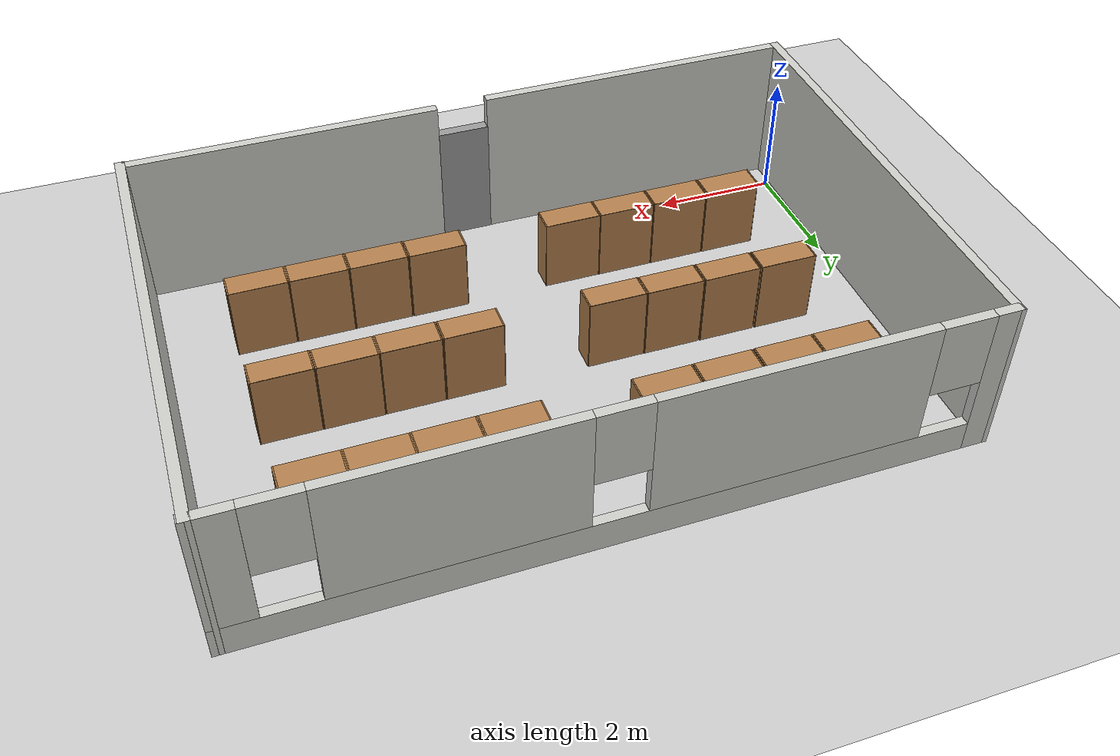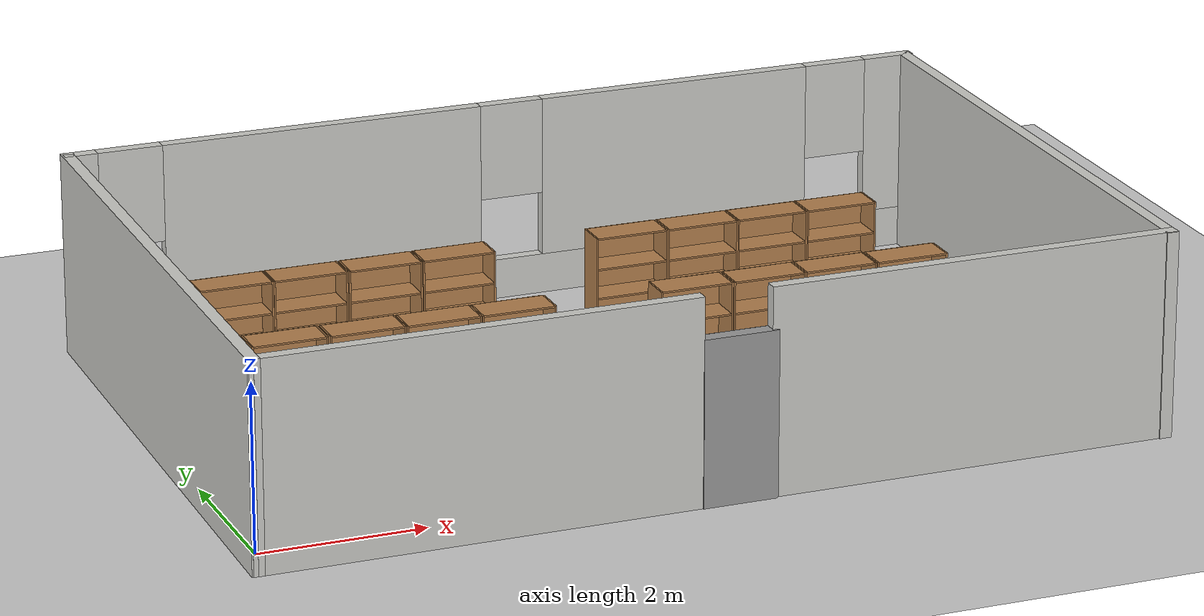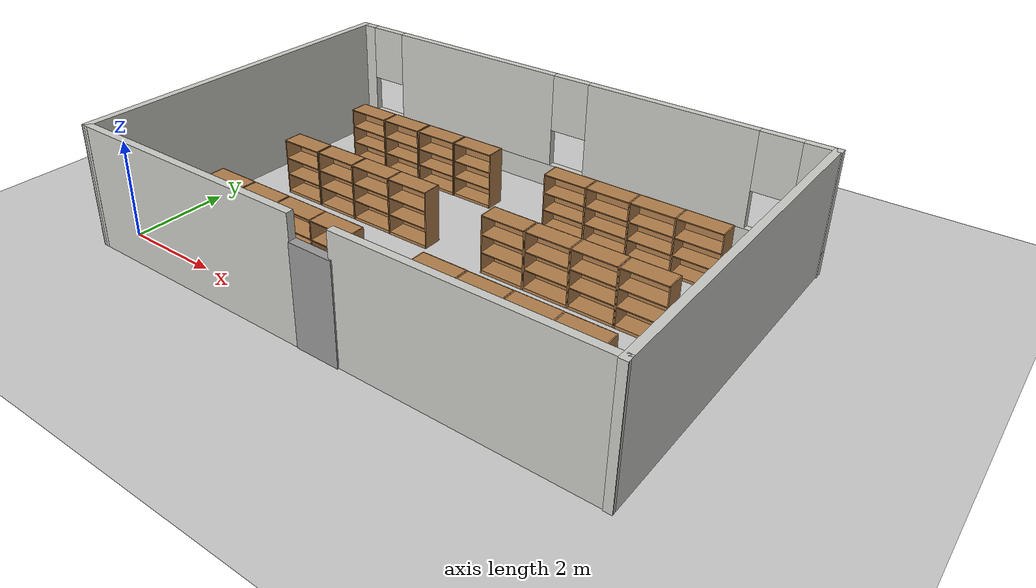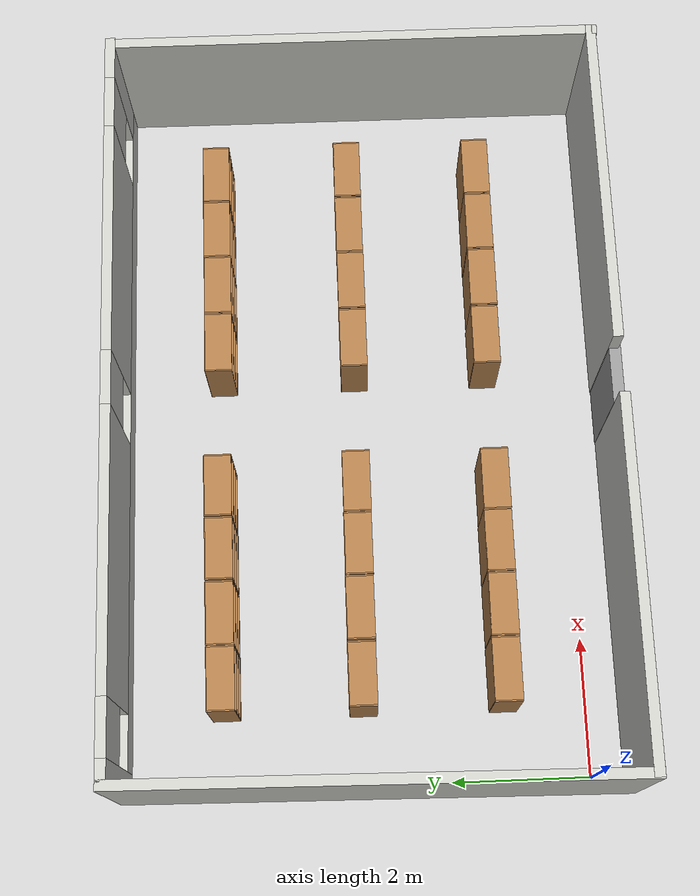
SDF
<sdf version="1.7">
 <world name="default">
  <scene><ambient>0.4 0.4 0.4 1</ambient><background>0.7 0.7 0.7 1</background><shadows>1</shadows></scene>
  <light name="sun" type="directional">
   <pose>0 0 10 0 -0 0</pose>
   <diffuse>0.8 0.8 0.8 1</diffuse>
   <specular>0.2 0.2 0.2 1</specular>
   <attenuation>
    <range>1000</range>
    <constant>0.9</constant>
    <linear>0.01</linear>
    <quadratic>0.001</quadratic>
   </attenuation>
   <direction>-0.5 0.1 -0.9</direction>
   <spot><inner_angle>0</inner_angle><outer_angle>0</outer_angle><falloff>0</falloff></spot>
  </light>
  <model name="ground_plane">
   <static>1</static>
   <link name="link">
    <collision name="collision">
     <geometry><plane><normal>0 0 1</normal><size>100 100</size></plane></geometry>
     <surface>
      <contact><collide_bitmask>65535</collide_bitmask></contact>
      <friction><ode><mu>100</mu><mu2>50</mu2></ode></friction>
     </surface>
    </collision>
    <visual name="visual">
     <cast_shadows>0</cast_shadows>
     <geometry><plane><normal>0 0 1</normal><size>100 100</size></plane></geometry>
     <material>
      <script><uri>file://media/materials/scripts/gazebo.material</uri><name>Gazebo/Grey</name></script>
     </material>
    </visual>
   </link>
  </model>
  <physics type="ode">
   <real_time_update_rate>1000</real_time_update_rate>
   <max_step_size>0.001</max_step_size>
   <real_time_factor>1</real_time_factor>
   <ode>
    <solver>
     <type>quick</type>
     <iters>150</iters>
     <precon_iters>0</precon_iters>
     <sor>1.4</sor>
     <use_dynamic_moi_rescaling>1</use_dynamic_moi_rescaling>
    </solver>
    <constraints>
     <cfm>1e-05</cfm>
     <erp>0.2</erp>
     <contact_max_correcting_vel>2000</contact_max_correcting_vel>
     <contact_surface_layer>0.01</contact_surface_layer>
    </constraints>
   </ode>
  </physics>
  <gravity>0 0 -9.8</gravity>
  <magnetic_field>6e-06 2.3e-05 -4.2e-05</magnetic_field>
  <atmosphere type="adiabatic"/>
  <audio><device>default</device></audio>
  <spherical_coordinates>
   <surface_model>EARTH_WGS84</surface_model>
   <latitude_deg>0</latitude_deg>
   <longitude_deg>0</longitude_deg>
   <elevation>0</elevation>
   <heading_deg>0</heading_deg>
  </spherical_coordinates>
  <model name="bookshelf">
   <static>1</static>
   <link name="link">
    <inertial><mass>1</mass></inertial>
    <collision name="back">
     <pose>0 0.005 0.6 0 -0 0</pose>
     <geometry><box><size>0.9 0.01 1.2</size></box></geometry>
    </collision>
    <visual name="visual1">
     <pose>0 0.005 0.6 0 -0 0</pose>
     <geometry><box><size>0.9 0.01 1.2</size></box></geometry>
     <material>
      <script><uri>file://media/materials/scripts/gazebo.material</uri><name>Gazebo/Wood</name></script>
     </material>
    </visual>
    <collision name="left_side">
     <pose>0.45 -0.195 0.6 0 -0 0</pose>
     <geometry><box><size>0.02 0.4 1.2</size></box></geometry>
    </collision>
    <visual name="visual2">
     <pose>0.45 -0.195 0.6 0 -0 0</pose>
     <geometry><box><size>0.02 0.4 1.2</size></box></geometry>
     <material>
      <script><uri>file://media/materials/scripts/gazebo.material</uri><name>Gazebo/Wood</name></script>
     </material>
    </visual>
    <collision name="right_side">
     <pose>-0.45 -0.195 0.6 0 -0 0</pose>
     <geometry><box><size>0.02 0.4 1.2</size></box></geometry>
    </collision>
    <visual name="visual3">
     <pose>-0.45 -0.195 0.6 0 -0 0</pose>
     <geometry><box><size>0.02 0.4 1.2</size></box></geometry>
     <material>
      <script><uri>file://media/materials/scripts/gazebo.material</uri><name>Gazebo/Wood</name></script>
     </material>
    </visual>
    <collision name="bottom">
     <pose>0 -0.195 0.03 0 -0 0</pose>
     <geometry><box><size>0.88 0.4 0.06</size></box></geometry>
    </collision>
    <visual name="visual4">
     <pose>0 -0.195 0.03 0 -0 0</pose>
     <geometry><box><size>0.88 0.4 0.06</size></box></geometry>
     <material>
      <script><uri>file://media/materials/scripts/gazebo.material</uri><name>Gazebo/Wood</name></script>
     </material>
    </visual>
    <collision name="top">
     <pose>0 -0.195 1.19 0 -0 0</pose>
     <geometry><box><size>0.88 0.4 0.02</size></box></geometry>
    </collision>
    <visual name="visual5">
     <pose>0 -0.195 1.19 0 -0 0</pose>
     <geometry><box><size>0.88 0.4 0.02</size></box></geometry>
     <material>
      <script><uri>file://media/materials/scripts/gazebo.material</uri><name>Gazebo/Wood</name></script>
     </material>
    </visual>
    <collision name="low_shelf">
     <pose>0 -0.195 0.43 0 -0 0</pose>
     <geometry><box><size>0.88 0.4 0.02</size></box></geometry>
    </collision>
    <visual name="visual6">
     <pose>0 -0.195 0.43 0 -0 0</pose>
     <geometry><box><size>0.88 0.4 0.02</size></box></geometry>
     <material>
      <script><uri>file://media/materials/scripts/gazebo.material</uri><name>Gazebo/Wood</name></script>
     </material>
    </visual>
    <collision name="high_shelf">
     <pose>0 -0.195 0.8 0 -0 0</pose>
     <geometry><box><size>0.88 0.4 0.02</size></box></geometry>
    </collision>
    <visual name="visual7">
     <pose>0 -0.195 0.8 0 -0 0</pose>
     <geometry><box><size>0.88 0.4 0.02</size></box></geometry>
     <material>
      <script><uri>file://media/materials/scripts/gazebo.material</uri><name>Gazebo/Wood</name></script>
     </material>
    </visual>
   </link>
   <pose>1.45184 3.43534 0 0 -0 0</pose>
  </model>
  <model name="bookshelf_0">
   <static>1</static>
   <link name="link">
    <inertial><mass>1</mass></inertial>
    <collision name="back">
     <pose>0 0.005 0.6 0 -0 0</pose>
     <geometry><box><size>0.9 0.01 1.2</size></box></geometry>
    </collision>
    <visual name="visual1">
     <pose>0 0.005 0.6 0 -0 0</pose>
     <geometry><box><size>0.9 0.01 1.2</size></box></geometry>
     <material>
      <script><uri>file://media/materials/scripts/gazebo.material</uri><name>Gazebo/Wood</name></script>
     </material>
    </visual>
    <collision name="left_side">
     <pose>0.45 -0.195 0.6 0 -0 0</pose>
     <geometry><box><size>0.02 0.4 1.2</size></box></geometry>
    </collision>
    <visual name="visual2">
     <pose>0.45 -0.195 0.6 0 -0 0</pose>
     <geometry><box><size>0.02 0.4 1.2</size></box></geometry>
     <material>
      <script><uri>file://media/materials/scripts/gazebo.material</uri><name>Gazebo/Wood</name></script>
     </material>
    </visual>
    <collision name="right_side">
     <pose>-0.45 -0.195 0.6 0 -0 0</pose>
     <geometry><box><size>0.02 0.4 1.2</size></box></geometry>
    </collision>
    <visual name="visual3">
     <pose>-0.45 -0.195 0.6 0 -0 0</pose>
     <geometry><box><size>0.02 0.4 1.2</size></box></geometry>
     <material>
      <script><uri>file://media/materials/scripts/gazebo.material</uri><name>Gazebo/Wood</name></script>
     </material>
    </visual>
    <collision name="bottom">
     <pose>0 -0.195 0.03 0 -0 0</pose>
     <geometry><box><size>0.88 0.4 0.06</size></box></geometry>
    </collision>
    <visual name="visual4">
     <pose>0 -0.195 0.03 0 -0 0</pose>
     <geometry><box><size>0.88 0.4 0.06</size></box></geometry>
     <material>
      <script><uri>file://media/materials/scripts/gazebo.material</uri><name>Gazebo/Wood</name></script>
     </material>
    </visual>
    <collision name="top">
     <pose>0 -0.195 1.19 0 -0 0</pose>
     <geometry><box><size>0.88 0.4 0.02</size></box></geometry>
    </collision>
    <visual name="visual5">
     <pose>0 -0.195 1.19 0 -0 0</pose>
     <geometry><box><size>0.88 0.4 0.02</size></box></geometry>
     <material>
      <script><uri>file://media/materials/scripts/gazebo.material</uri><name>Gazebo/Wood</name></script>
     </material>
    </visual>
    <collision name="low_shelf">
     <pose>0 -0.195 0.43 0 -0 0</pose>
     <geometry><box><size>0.88 0.4 0.02</size></box></geometry>
    </collision>
    <visual name="visual6">
     <pose>0 -0.195 0.43 0 -0 0</pose>
     <geometry><box><size>0.88 0.4 0.02</size></box></geometry>
     <material>
      <script><uri>file://media/materials/scripts/gazebo.material</uri><name>Gazebo/Wood</name></script>
     </material>
    </visual>
    <collision name="high_shelf">
     <pose>0 -0.195 0.8 0 -0 0</pose>
     <geometry><box><size>0.88 0.4 0.02</size></box></geometry>
    </collision>
    <visual name="visual7">
     <pose>0 -0.195 0.8 0 -0 0</pose>
     <geometry><box><size>0.88 0.4 0.02</size></box></geometry>
     <material>
      <script><uri>file://media/materials/scripts/gazebo.material</uri><name>Gazebo/Wood</name></script>
     </material>
    </visual>
   </link>
   <pose>2.39092 3.43134 0 0 -0 0</pose>
  </model>
  <model name="bookshelf_1">
   <static>1</static>
   <link name="link">
    <inertial><mass>1</mass></inertial>
    <collision name="back">
     <pose>0 0.005 0.6 0 -0 0</pose>
     <geometry><box><size>0.9 0.01 1.2</size></box></geometry>
    </collision>
    <visual name="visual1">
     <pose>0 0.005 0.6 0 -0 0</pose>
     <geometry><box><size>0.9 0.01 1.2</size></box></geometry>
     <material>
      <script><uri>file://media/materials/scripts/gazebo.material</uri><name>Gazebo/Wood</name></script>
     </material>
    </visual>
    <collision name="left_side">
     <pose>0.45 -0.195 0.6 0 -0 0</pose>
     <geometry><box><size>0.02 0.4 1.2</size></box></geometry>
    </collision>
    <visual name="visual2">
     <pose>0.45 -0.195 0.6 0 -0 0</pose>
     <geometry><box><size>0.02 0.4 1.2</size></box></geometry>
     <material>
      <script><uri>file://media/materials/scripts/gazebo.material</uri><name>Gazebo/Wood</name></script>
     </material>
    </visual>
    <collision name="right_side">
     <pose>-0.45 -0.195 0.6 0 -0 0</pose>
     <geometry><box><size>0.02 0.4 1.2</size></box></geometry>
    </collision>
    <visual name="visual3">
     <pose>-0.45 -0.195 0.6 0 -0 0</pose>
     <geometry><box><size>0.02 0.4 1.2</size></box></geometry>
     <material>
      <script><uri>file://media/materials/scripts/gazebo.material</uri><name>Gazebo/Wood</name></script>
     </material>
    </visual>
    <collision name="bottom">
     <pose>0 -0.195 0.03 0 -0 0</pose>
     <geometry><box><size>0.88 0.4 0.06</size></box></geometry>
    </collision>
    <visual name="visual4">
     <pose>0 -0.195 0.03 0 -0 0</pose>
     <geometry><box><size>0.88 0.4 0.06</size></box></geometry>
     <material>
      <script><uri>file://media/materials/scripts/gazebo.material</uri><name>Gazebo/Wood</name></script>
     </material>
    </visual>
    <collision name="top">
     <pose>0 -0.195 1.19 0 -0 0</pose>
     <geometry><box><size>0.88 0.4 0.02</size></box></geometry>
    </collision>
    <visual name="visual5">
     <pose>0 -0.195 1.19 0 -0 0</pose>
     <geometry><box><size>0.88 0.4 0.02</size></box></geometry>
     <material>
      <script><uri>file://media/materials/scripts/gazebo.material</uri><name>Gazebo/Wood</name></script>
     </material>
    </visual>
    <collision name="low_shelf">
     <pose>0 -0.195 0.43 0 -0 0</pose>
     <geometry><box><size>0.88 0.4 0.02</size></box></geometry>
    </collision>
    <visual name="visual6">
     <pose>0 -0.195 0.43 0 -0 0</pose>
     <geometry><box><size>0.88 0.4 0.02</size></box></geometry>
     <material>
      <script><uri>file://media/materials/scripts/gazebo.material</uri><name>Gazebo/Wood</name></script>
     </material>
    </visual>
    <collision name="high_shelf">
     <pose>0 -0.195 0.8 0 -0 0</pose>
     <geometry><box><size>0.88 0.4 0.02</size></box></geometry>
    </collision>
    <visual name="visual7">
     <pose>0 -0.195 0.8 0 -0 0</pose>
     <geometry><box><size>0.88 0.4 0.02</size></box></geometry>
     <material>
      <script><uri>file://media/materials/scripts/gazebo.material</uri><name>Gazebo/Wood</name></script>
     </material>
    </visual>
   </link>
   <pose>3.31925 3.42546 0 0 -0 0</pose>
  </model>
  <model name="bookshelf_2">
   <static>1</static>
   <link name="link">
    <inertial><mass>1</mass></inertial>
    <collision name="back">
     <pose>0 0.005 0.6 0 -0 0</pose>
     <geometry><box><size>0.9 0.01 1.2</size></box></geometry>
    </collision>
    <visual name="visual1">
     <pose>0 0.005 0.6 0 -0 0</pose>
     <geometry><box><size>0.9 0.01 1.2</size></box></geometry>
     <material>
      <script><uri>file://media/materials/scripts/gazebo.material</uri><name>Gazebo/Wood</name></script>
     </material>
    </visual>
    <collision name="left_side">
     <pose>0.45 -0.195 0.6 0 -0 0</pose>
     <geometry><box><size>0.02 0.4 1.2</size></box></geometry>
    </collision>
    <visual name="visual2">
     <pose>0.45 -0.195 0.6 0 -0 0</pose>
     <geometry><box><size>0.02 0.4 1.2</size></box></geometry>
     <material>
      <script><uri>file://media/materials/scripts/gazebo.material</uri><name>Gazebo/Wood</name></script>
     </material>
    </visual>
    <collision name="right_side">
     <pose>-0.45 -0.195 0.6 0 -0 0</pose>
     <geometry><box><size>0.02 0.4 1.2</size></box></geometry>
    </collision>
    <visual name="visual3">
     <pose>-0.45 -0.195 0.6 0 -0 0</pose>
     <geometry><box><size>0.02 0.4 1.2</size></box></geometry>
     <material>
      <script><uri>file://media/materials/scripts/gazebo.material</uri><name>Gazebo/Wood</name></script>
     </material>
    </visual>
    <collision name="bottom">
     <pose>0 -0.195 0.03 0 -0 0</pose>
     <geometry><box><size>0.88 0.4 0.06</size></box></geometry>
    </collision>
    <visual name="visual4">
     <pose>0 -0.195 0.03 0 -0 0</pose>
     <geometry><box><size>0.88 0.4 0.06</size></box></geometry>
     <material>
      <script><uri>file://media/materials/scripts/gazebo.material</uri><name>Gazebo/Wood</name></script>
     </material>
    </visual>
    <collision name="top">
     <pose>0 -0.195 1.19 0 -0 0</pose>
     <geometry><box><size>0.88 0.4 0.02</size></box></geometry>
    </collision>
    <visual name="visual5">
     <pose>0 -0.195 1.19 0 -0 0</pose>
     <geometry><box><size>0.88 0.4 0.02</size></box></geometry>
     <material>
      <script><uri>file://media/materials/scripts/gazebo.material</uri><name>Gazebo/Wood</name></script>
     </material>
    </visual>
    <collision name="low_shelf">
     <pose>0 -0.195 0.43 0 -0 0</pose>
     <geometry><box><size>0.88 0.4 0.02</size></box></geometry>
    </collision>
    <visual name="visual6">
     <pose>0 -0.195 0.43 0 -0 0</pose>
     <geometry><box><size>0.88 0.4 0.02</size></box></geometry>
     <material>
      <script><uri>file://media/materials/scripts/gazebo.material</uri><name>Gazebo/Wood</name></script>
     </material>
    </visual>
    <collision name="high_shelf">
     <pose>0 -0.195 0.8 0 -0 0</pose>
     <geometry><box><size>0.88 0.4 0.02</size></box></geometry>
    </collision>
    <visual name="visual7">
     <pose>0 -0.195 0.8 0 -0 0</pose>
     <geometry><box><size>0.88 0.4 0.02</size></box></geometry>
     <material>
      <script><uri>file://media/materials/scripts/gazebo.material</uri><name>Gazebo/Wood</name></script>
     </material>
    </visual>
   </link>
   <pose>4.24207 3.42066 0 0 -0 0</pose>
  </model>
  <model name="bookshelf_3">
   <static>1</static>
   <link name="link">
    <inertial><mass>1</mass></inertial>
    <collision name="back">
     <pose>0 0.005 0.6 0 -0 0</pose>
     <geometry><box><size>0.9 0.01 1.2</size></box></geometry>
    </collision>
    <visual name="visual1">
     <pose>0 0.005 0.6 0 -0 0</pose>
     <geometry><box><size>0.9 0.01 1.2</size></box></geometry>
     <material>
      <script><uri>file://media/materials/scripts/gazebo.material</uri><name>Gazebo/Wood</name></script>
     </material>
    </visual>
    <collision name="left_side">
     <pose>0.45 -0.195 0.6 0 -0 0</pose>
     <geometry><box><size>0.02 0.4 1.2</size></box></geometry>
    </collision>
    <visual name="visual2">
     <pose>0.45 -0.195 0.6 0 -0 0</pose>
     <geometry><box><size>0.02 0.4 1.2</size></box></geometry>
     <material>
      <script><uri>file://media/materials/scripts/gazebo.material</uri><name>Gazebo/Wood</name></script>
     </material>
    </visual>
    <collision name="right_side">
     <pose>-0.45 -0.195 0.6 0 -0 0</pose>
     <geometry><box><size>0.02 0.4 1.2</size></box></geometry>
    </collision>
    <visual name="visual3">
     <pose>-0.45 -0.195 0.6 0 -0 0</pose>
     <geometry><box><size>0.02 0.4 1.2</size></box></geometry>
     <material>
      <script><uri>file://media/materials/scripts/gazebo.material</uri><name>Gazebo/Wood</name></script>
     </material>
    </visual>
    <collision name="bottom">
     <pose>0 -0.195 0.03 0 -0 0</pose>
     <geometry><box><size>0.88 0.4 0.06</size></box></geometry>
    </collision>
    <visual name="visual4">
     <pose>0 -0.195 0.03 0 -0 0</pose>
     <geometry><box><size>0.88 0.4 0.06</size></box></geometry>
     <material>
      <script><uri>file://media/materials/scripts/gazebo.material</uri><name>Gazebo/Wood</name></script>
     </material>
    </visual>
    <collision name="top">
     <pose>0 -0.195 1.19 0 -0 0</pose>
     <geometry><box><size>0.88 0.4 0.02</size></box></geometry>
    </collision>
    <visual name="visual5">
     <pose>0 -0.195 1.19 0 -0 0</pose>
     <geometry><box><size>0.88 0.4 0.02</size></box></geometry>
     <material>
      <script><uri>file://media/materials/scripts/gazebo.material</uri><name>Gazebo/Wood</name></script>
     </material>
    </visual>
    <collision name="low_shelf">
     <pose>0 -0.195 0.43 0 -0 0</pose>
     <geometry><box><size>0.88 0.4 0.02</size></box></geometry>
    </collision>
    <visual name="visual6">
     <pose>0 -0.195 0.43 0 -0 0</pose>
     <geometry><box><size>0.88 0.4 0.02</size></box></geometry>
     <material>
      <script><uri>file://media/materials/scripts/gazebo.material</uri><name>Gazebo/Wood</name></script>
     </material>
    </visual>
    <collision name="high_shelf">
     <pose>0 -0.195 0.8 0 -0 0</pose>
     <geometry><box><size>0.88 0.4 0.02</size></box></geometry>
    </collision>
    <visual name="visual7">
     <pose>0 -0.195 0.8 0 -0 0</pose>
     <geometry><box><size>0.88 0.4 0.02</size></box></geometry>
     <material>
      <script><uri>file://media/materials/scripts/gazebo.material</uri><name>Gazebo/Wood</name></script>
     </material>
    </visual>
   </link>
   <pose>1.4441 1.40563 0 -0.000728 0 0</pose>
  </model>
  <model name="bookshelf_4">
   <static>1</static>
   <link name="link">
    <inertial><mass>1</mass></inertial>
    <collision name="back">
     <pose>0 0.005 0.6 0 -0 0</pose>
     <geometry><box><size>0.9 0.01 1.2</size></box></geometry>
    </collision>
    <visual name="visual1">
     <pose>0 0.005 0.6 0 -0 0</pose>
     <geometry><box><size>0.9 0.01 1.2</size></box></geometry>
     <material>
      <script><uri>file://media/materials/scripts/gazebo.material</uri><name>Gazebo/Wood</name></script>
     </material>
    </visual>
    <collision name="left_side">
     <pose>0.45 -0.195 0.6 0 -0 0</pose>
     <geometry><box><size>0.02 0.4 1.2</size></box></geometry>
    </collision>
    <visual name="visual2">
     <pose>0.45 -0.195 0.6 0 -0 0</pose>
     <geometry><box><size>0.02 0.4 1.2</size></box></geometry>
     <material>
      <script><uri>file://media/materials/scripts/gazebo.material</uri><name>Gazebo/Wood</name></script>
     </material>
    </visual>
    <collision name="right_side">
     <pose>-0.45 -0.195 0.6 0 -0 0</pose>
     <geometry><box><size>0.02 0.4 1.2</size></box></geometry>
    </collision>
    <visual name="visual3">
     <pose>-0.45 -0.195 0.6 0 -0 0</pose>
     <geometry><box><size>0.02 0.4 1.2</size></box></geometry>
     <material>
      <script><uri>file://media/materials/scripts/gazebo.material</uri><name>Gazebo/Wood</name></script>
     </material>
    </visual>
    <collision name="bottom">
     <pose>0 -0.195 0.03 0 -0 0</pose>
     <geometry><box><size>0.88 0.4 0.06</size></box></geometry>
    </collision>
    <visual name="visual4">
     <pose>0 -0.195 0.03 0 -0 0</pose>
     <geometry><box><size>0.88 0.4 0.06</size></box></geometry>
     <material>
      <script><uri>file://media/materials/scripts/gazebo.material</uri><name>Gazebo/Wood</name></script>
     </material>
    </visual>
    <collision name="top">
     <pose>0 -0.195 1.19 0 -0 0</pose>
     <geometry><box><size>0.88 0.4 0.02</size></box></geometry>
    </collision>
    <visual name="visual5">
     <pose>0 -0.195 1.19 0 -0 0</pose>
     <geometry><box><size>0.88 0.4 0.02</size></box></geometry>
     <material>
      <script><uri>file://media/materials/scripts/gazebo.material</uri><name>Gazebo/Wood</name></script>
     </material>
    </visual>
    <collision name="low_shelf">
     <pose>0 -0.195 0.43 0 -0 0</pose>
     <geometry><box><size>0.88 0.4 0.02</size></box></geometry>
    </collision>
    <visual name="visual6">
     <pose>0 -0.195 0.43 0 -0 0</pose>
     <geometry><box><size>0.88 0.4 0.02</size></box></geometry>
     <material>
      <script><uri>file://media/materials/scripts/gazebo.material</uri><name>Gazebo/Wood</name></script>
     </material>
    </visual>
    <collision name="high_shelf">
     <pose>0 -0.195 0.8 0 -0 0</pose>
     <geometry><box><size>0.88 0.4 0.02</size></box></geometry>
    </collision>
    <visual name="visual7">
     <pose>0 -0.195 0.8 0 -0 0</pose>
     <geometry><box><size>0.88 0.4 0.02</size></box></geometry>
     <material>
      <script><uri>file://media/materials/scripts/gazebo.material</uri><name>Gazebo/Wood</name></script>
     </material>
    </visual>
   </link>
   <pose>2.36984 1.40261 0 0 -0 0</pose>
  </model>
  <model name="bookshelf_5">
   <static>1</static>
   <link name="link">
    <inertial><mass>1</mass></inertial>
    <collision name="back">
     <pose>0 0.005 0.6 0 -0 0</pose>
     <geometry><box><size>0.9 0.01 1.2</size></box></geometry>
    </collision>
    <visual name="visual1">
     <pose>0 0.005 0.6 0 -0 0</pose>
     <geometry><box><size>0.9 0.01 1.2</size></box></geometry>
     <material>
      <script><uri>file://media/materials/scripts/gazebo.material</uri><name>Gazebo/Wood</name></script>
     </material>
    </visual>
    <collision name="left_side">
     <pose>0.45 -0.195 0.6 0 -0 0</pose>
     <geometry><box><size>0.02 0.4 1.2</size></box></geometry>
    </collision>
    <visual name="visual2">
     <pose>0.45 -0.195 0.6 0 -0 0</pose>
     <geometry><box><size>0.02 0.4 1.2</size></box></geometry>
     <material>
      <script><uri>file://media/materials/scripts/gazebo.material</uri><name>Gazebo/Wood</name></script>
     </material>
    </visual>
    <collision name="right_side">
     <pose>-0.45 -0.195 0.6 0 -0 0</pose>
     <geometry><box><size>0.02 0.4 1.2</size></box></geometry>
    </collision>
    <visual name="visual3">
     <pose>-0.45 -0.195 0.6 0 -0 0</pose>
     <geometry><box><size>0.02 0.4 1.2</size></box></geometry>
     <material>
      <script><uri>file://media/materials/scripts/gazebo.material</uri><name>Gazebo/Wood</name></script>
     </material>
    </visual>
    <collision name="bottom">
     <pose>0 -0.195 0.03 0 -0 0</pose>
     <geometry><box><size>0.88 0.4 0.06</size></box></geometry>
    </collision>
    <visual name="visual4">
     <pose>0 -0.195 0.03 0 -0 0</pose>
     <geometry><box><size>0.88 0.4 0.06</size></box></geometry>
     <material>
      <script><uri>file://media/materials/scripts/gazebo.material</uri><name>Gazebo/Wood</name></script>
     </material>
    </visual>
    <collision name="top">
     <pose>0 -0.195 1.19 0 -0 0</pose>
     <geometry><box><size>0.88 0.4 0.02</size></box></geometry>
    </collision>
    <visual name="visual5">
     <pose>0 -0.195 1.19 0 -0 0</pose>
     <geometry><box><size>0.88 0.4 0.02</size></box></geometry>
     <material>
      <script><uri>file://media/materials/scripts/gazebo.material</uri><name>Gazebo/Wood</name></script>
     </material>
    </visual>
    <collision name="low_shelf">
     <pose>0 -0.195 0.43 0 -0 0</pose>
     <geometry><box><size>0.88 0.4 0.02</size></box></geometry>
    </collision>
    <visual name="visual6">
     <pose>0 -0.195 0.43 0 -0 0</pose>
     <geometry><box><size>0.88 0.4 0.02</size></box></geometry>
     <material>
      <script><uri>file://media/materials/scripts/gazebo.material</uri><name>Gazebo/Wood</name></script>
     </material>
    </visual>
    <collision name="high_shelf">
     <pose>0 -0.195 0.8 0 -0 0</pose>
     <geometry><box><size>0.88 0.4 0.02</size></box></geometry>
    </collision>
    <visual name="visual7">
     <pose>0 -0.195 0.8 0 -0 0</pose>
     <geometry><box><size>0.88 0.4 0.02</size></box></geometry>
     <material>
      <script><uri>file://media/materials/scripts/gazebo.material</uri><name>Gazebo/Wood</name></script>
     </material>
    </visual>
   </link>
   <pose>3.29308 1.40142 0 0 -0 0</pose>
  </model>
  <model name="bookshelf_6">
   <static>1</static>
   <link name="link">
    <inertial><mass>1</mass></inertial>
    <collision name="back">
     <pose>0 0.005 0.6 0 -0 0</pose>
     <geometry><box><size>0.9 0.01 1.2</size></box></geometry>
    </collision>
    <visual name="visual1">
     <pose>0 0.005 0.6 0 -0 0</pose>
     <geometry><box><size>0.9 0.01 1.2</size></box></geometry>
     <material>
      <script><uri>file://media/materials/scripts/gazebo.material</uri><name>Gazebo/Wood</name></script>
     </material>
    </visual>
    <collision name="left_side">
     <pose>0.45 -0.195 0.6 0 -0 0</pose>
     <geometry><box><size>0.02 0.4 1.2</size></box></geometry>
    </collision>
    <visual name="visual2">
     <pose>0.45 -0.195 0.6 0 -0 0</pose>
     <geometry><box><size>0.02 0.4 1.2</size></box></geometry>
     <material>
      <script><uri>file://media/materials/scripts/gazebo.material</uri><name>Gazebo/Wood</name></script>
     </material>
    </visual>
    <collision name="right_side">
     <pose>-0.45 -0.195 0.6 0 -0 0</pose>
     <geometry><box><size>0.02 0.4 1.2</size></box></geometry>
    </collision>
    <visual name="visual3">
     <pose>-0.45 -0.195 0.6 0 -0 0</pose>
     <geometry><box><size>0.02 0.4 1.2</size></box></geometry>
     <material>
      <script><uri>file://media/materials/scripts/gazebo.material</uri><name>Gazebo/Wood</name></script>
     </material>
    </visual>
    <collision name="bottom">
     <pose>0 -0.195 0.03 0 -0 0</pose>
     <geometry><box><size>0.88 0.4 0.06</size></box></geometry>
    </collision>
    <visual name="visual4">
     <pose>0 -0.195 0.03 0 -0 0</pose>
     <geometry><box><size>0.88 0.4 0.06</size></box></geometry>
     <material>
      <script><uri>file://media/materials/scripts/gazebo.material</uri><name>Gazebo/Wood</name></script>
     </material>
    </visual>
    <collision name="top">
     <pose>0 -0.195 1.19 0 -0 0</pose>
     <geometry><box><size>0.88 0.4 0.02</size></box></geometry>
    </collision>
    <visual name="visual5">
     <pose>0 -0.195 1.19 0 -0 0</pose>
     <geometry><box><size>0.88 0.4 0.02</size></box></geometry>
     <material>
      <script><uri>file://media/materials/scripts/gazebo.material</uri><name>Gazebo/Wood</name></script>
     </material>
    </visual>
    <collision name="low_shelf">
     <pose>0 -0.195 0.43 0 -0 0</pose>
     <geometry><box><size>0.88 0.4 0.02</size></box></geometry>
    </collision>
    <visual name="visual6">
     <pose>0 -0.195 0.43 0 -0 0</pose>
     <geometry><box><size>0.88 0.4 0.02</size></box></geometry>
     <material>
      <script><uri>file://media/materials/scripts/gazebo.material</uri><name>Gazebo/Wood</name></script>
     </material>
    </visual>
    <collision name="high_shelf">
     <pose>0 -0.195 0.8 0 -0 0</pose>
     <geometry><box><size>0.88 0.4 0.02</size></box></geometry>
    </collision>
    <visual name="visual7">
     <pose>0 -0.195 0.8 0 -0 0</pose>
     <geometry><box><size>0.88 0.4 0.02</size></box></geometry>
     <material>
      <script><uri>file://media/materials/scripts/gazebo.material</uri><name>Gazebo/Wood</name></script>
     </material>
    </visual>
   </link>
   <pose>4.20808 1.39756 0 0 -0 0</pose>
  </model>
  <model name="beer">
   <link name="link">
    <pose>0 0 0.115 0 -0 0</pose>
    <inertial>
     <mass>0.39</mass>
     <inertia><ixx>0.00058</ixx><ixy>0</ixy><ixz>0</ixz><iyy>0.00058</iyy><iyz>0</iyz><izz>0.00019</izz></inertia>
    </inertial>
    <collision name="collision">
     <geometry><cylinder><radius>0.055</radius><length>0.23</length></cylinder></geometry>
    </collision>
    <visual name="visual">
     <geometry><cylinder><radius>0.055</radius><length>0.23</length></cylinder></geometry>
     <material>
      <script>
       <uri>model://beer/materials/scripts</uri>
       <uri>model://beer/materials/textures</uri>
       <name>Beer/Diffuse</name>
      </script>
     </material>
    </visual>
   </link>
   <pose>1.07644 1.3497 0.810032 -0.000731 -1e-05 0.001882</pose>
  </model>
  <model name="beer_0">
   <link name="link">
    <pose>0 0 0.115 0 -0 0</pose>
    <inertial>
     <mass>0.39</mass>
     <inertia><ixx>0.00058</ixx><ixy>0</ixy><ixz>0</ixz><iyy>0.00058</iyy><iyz>0</iyz><izz>0.00019</izz></inertia>
    </inertial>
    <collision name="collision">
     <geometry><cylinder><radius>0.055</radius><length>0.23</length></cylinder></geometry>
    </collision>
    <visual name="visual">
     <geometry><cylinder><radius>0.055</radius><length>0.23</length></cylinder></geometry>
     <material>
      <script>
       <uri>model://beer/materials/scripts</uri>
       <uri>model://beer/materials/textures</uri>
       <name>Beer/Diffuse</name>
      </script>
     </material>
    </visual>
   </link>
   <pose>1.07637 1.09987 0.810226 -0.00078 -3e-06 0.001772</pose>
  </model>
  <model name="beer_1">
   <link name="link">
    <pose>0 0 0.115 0 -0 0</pose>
    <inertial>
     <mass>0.39</mass>
     <inertia><ixx>0.00058</ixx><ixy>0</ixy><ixz>0</ixz><iyy>0.00058</iyy><iyz>0</iyz><izz>0.00019</izz></inertia>
    </inertial>
    <collision name="collision">
     <geometry><cylinder><radius>0.055</radius><length>0.23</length></cylinder></geometry>
    </collision>
    <visual name="visual">
     <geometry><cylinder><radius>0.055</radius><length>0.23</length></cylinder></geometry>
     <material>
      <script>
       <uri>model://beer/materials/scripts</uri>
       <uri>model://beer/materials/textures</uri>
       <name>Beer/Diffuse</name>
      </script>
     </material>
    </visual>
   </link>
   <pose>1.23236 1.33918 0.810039 -0.000739 -2e-06 0.001984</pose>
  </model>
  <model name="beer_2">
   <link name="link">
    <pose>0 0 0.115 0 -0 0</pose>
    <inertial>
     <mass>0.39</mass>
     <inertia><ixx>0.00058</ixx><ixy>0</ixy><ixz>0</ixz><iyy>0.00058</iyy><iyz>0</iyz><izz>0.00019</izz></inertia>
    </inertial>
    <collision name="collision">
     <geometry><cylinder><radius>0.055</radius><length>0.23</length></cylinder></geometry>
    </collision>
    <visual name="visual">
     <geometry><cylinder><radius>0.055</radius><length>0.23</length></cylinder></geometry>
     <material>
      <script>
       <uri>model://beer/materials/scripts</uri>
       <uri>model://beer/materials/textures</uri>
       <name>Beer/Diffuse</name>
      </script>
     </material>
    </visual>
   </link>
   <pose>1.24062 1.1132 0.810215 -0.000755 0 0.001012</pose>
  </model>
  <model name="beer_3">
   <link name="link">
    <pose>0 0 0.115 0 -0 0</pose>
    <inertial>
     <mass>0.39</mass>
     <inertia><ixx>0.00058</ixx><ixy>0</ixy><ixz>0</ixz><iyy>0.00058</iyy><iyz>0</iyz><izz>0.00019</izz></inertia>
    </inertial>
    <collision name="collision">
     <geometry><cylinder><radius>0.055</radius><length>0.23</length></cylinder></geometry>
    </collision>
    <visual name="visual">
     <geometry><cylinder><radius>0.055</radius><length>0.23</length></cylinder></geometry>
     <material>
      <script>
       <uri>model://beer/materials/scripts</uri>
       <uri>model://beer/materials/textures</uri>
       <name>Beer/Diffuse</name>
      </script>
     </material>
    </visual>
   </link>
   <pose>1.37254 1.34323 0.810046 -0.000727 1e-06 0.00156</pose>
  </model>
  <model name="beer_4">
   <link name="link">
    <pose>0 0 0.115 0 -0 0</pose>
    <inertial>
     <mass>0.39</mass>
     <inertia><ixx>0.00058</ixx><ixy>0</ixy><ixz>0</ixz><iyy>0.00058</iyy><iyz>0</iyz><izz>0.00019</izz></inertia>
    </inertial>
    <collision name="collision">
     <geometry><cylinder><radius>0.055</radius><length>0.23</length></cylinder></geometry>
    </collision>
    <visual name="visual">
     <geometry><cylinder><radius>0.055</radius><length>0.23</length></cylinder></geometry>
     <material>
      <script>
       <uri>model://beer/materials/scripts</uri>
       <uri>model://beer/materials/textures</uri>
       <name>Beer/Diffuse</name>
      </script>
     </material>
    </visual>
   </link>
   <pose>1.37423 1.12022 0.810213 -0.000824 -4e-06 0.00107</pose>
  </model>
  <model name="beer_7">
   <link name="link">
    <pose>0 0 0.115 0 -0 0</pose>
    <inertial>
     <mass>0.39</mass>
     <inertia><ixx>0.00058</ixx><ixy>0</ixy><ixz>0</ixz><iyy>0.00058</iyy><iyz>0</iyz><izz>0.00019</izz></inertia>
    </inertial>
    <collision name="collision">
     <geometry><cylinder><radius>0.055</radius><length>0.23</length></cylinder></geometry>
    </collision>
    <visual name="visual">
     <geometry><cylinder><radius>0.055</radius><length>0.23</length></cylinder></geometry>
     <material>
      <script>
       <uri>model://beer/materials/scripts</uri>
       <uri>model://beer/materials/textures</uri>
       <name>Beer/Diffuse</name>
      </script>
     </material>
    </visual>
   </link>
   <pose>1.63489 1.24799 0.81012 -0.000824 -2e-06 0.002456</pose>
  </model>
  <model name="beer_8">
   <link name="link">
    <pose>0 0 0.115 0 -0 0</pose>
    <inertial>
     <mass>0.39</mass>
     <inertia><ixx>0.00058</ixx><ixy>0</ixy><ixz>0</ixz><iyy>0.00058</iyy><iyz>0</iyz><izz>0.00019</izz></inertia>
    </inertial>
    <collision name="collision">
     <geometry><cylinder><radius>0.055</radius><length>0.23</length></cylinder></geometry>
    </collision>
    <visual name="visual">
     <geometry><cylinder><radius>0.055</radius><length>0.23</length></cylinder></geometry>
     <material>
      <script>
       <uri>model://beer/materials/scripts</uri>
       <uri>model://beer/materials/textures</uri>
       <name>Beer/Diffuse</name>
      </script>
     </material>
    </visual>
   </link>
   <pose>1.64383 1.09075 0.810223 -0.000786 -0 6.7e-05</pose>
  </model>
  <model name="beer_9">
   <link name="link">
    <pose>0 0 0.115 0 -0 0</pose>
    <inertial>
     <mass>0.39</mass>
     <inertia><ixx>0.00058</ixx><ixy>0</ixy><ixz>0</ixz><iyy>0.00058</iyy><iyz>0</iyz><izz>0.00019</izz></inertia>
    </inertial>
    <collision name="collision">
     <geometry><cylinder><radius>0.055</radius><length>0.23</length></cylinder></geometry>
    </collision>
    <visual name="visual">
     <geometry><cylinder><radius>0.055</radius><length>0.23</length></cylinder></geometry>
     <material>
      <script>
       <uri>model://beer/materials/scripts</uri>
       <uri>model://beer/materials/textures</uri>
       <name>Beer/Diffuse</name>
      </script>
     </material>
    </visual>
   </link>
   <pose>1.79747 1.34026 0.810053 -0.000821 5e-06 0.003795</pose>
  </model>
  <model name="beer_10">
   <link name="link">
    <pose>0 0 0.115 0 -0 0</pose>
    <inertial>
     <mass>0.39</mass>
     <inertia><ixx>0.00058</ixx><ixy>0</ixy><ixz>0</ixz><iyy>0.00058</iyy><iyz>0</iyz><izz>0.00019</izz></inertia>
    </inertial>
    <collision name="collision">
     <geometry><cylinder><radius>0.055</radius><length>0.23</length></cylinder></geometry>
    </collision>
    <visual name="visual">
     <geometry><cylinder><radius>0.055</radius><length>0.23</length></cylinder></geometry>
     <material>
      <script>
       <uri>model://beer/materials/scripts</uri>
       <uri>model://beer/materials/textures</uri>
       <name>Beer/Diffuse</name>
      </script>
     </material>
    </visual>
   </link>
   <pose>1.78444 1.13593 0.8102 -0.000788 -2e-06 -0.000194</pose>
  </model>
  <model name="beer_5">
   <link name="link">
    <pose>0 0 0.115 0 -0 0</pose>
    <inertial>
     <mass>0.39</mass>
     <inertia><ixx>0.00058</ixx><ixy>0</ixy><ixz>0</ixz><iyy>0.00058</iyy><iyz>0</iyz><izz>0.00019</izz></inertia>
    </inertial>
    <collision name="collision">
     <geometry><cylinder><radius>0.055</radius><length>0.23</length></cylinder></geometry>
    </collision>
    <visual name="visual">
     <geometry><cylinder><radius>0.055</radius><length>0.23</length></cylinder></geometry>
     <material>
      <script>
       <uri>model://beer/materials/scripts</uri>
       <uri>model://beer/materials/textures</uri>
       <name>Beer/Diffuse</name>
      </script>
     </material>
    </visual>
   </link>
   <pose>1.5002 1.10253 0.810224 -0.000786 -3e-06 0.000126</pose>
  </model>
  <model name="bookshelf_7">
   <static>1</static>
   <link name="link">
    <inertial><mass>1</mass></inertial>
    <collision name="back">
     <pose>0 0.005 0.6 0 -0 0</pose>
     <geometry><box><size>0.9 0.01 1.2</size></box></geometry>
    </collision>
    <visual name="visual1">
     <pose>0 0.005 0.6 0 -0 0</pose>
     <geometry><box><size>0.9 0.01 1.2</size></box></geometry>
     <material>
      <script><uri>file://media/materials/scripts/gazebo.material</uri><name>Gazebo/Wood</name></script>
     </material>
    </visual>
    <collision name="left_side">
     <pose>0.45 -0.195 0.6 0 -0 0</pose>
     <geometry><box><size>0.02 0.4 1.2</size></box></geometry>
    </collision>
    <visual name="visual2">
     <pose>0.45 -0.195 0.6 0 -0 0</pose>
     <geometry><box><size>0.02 0.4 1.2</size></box></geometry>
     <material>
      <script><uri>file://media/materials/scripts/gazebo.material</uri><name>Gazebo/Wood</name></script>
     </material>
    </visual>
    <collision name="right_side">
     <pose>-0.45 -0.195 0.6 0 -0 0</pose>
     <geometry><box><size>0.02 0.4 1.2</size></box></geometry>
    </collision>
    <visual name="visual3">
     <pose>-0.45 -0.195 0.6 0 -0 0</pose>
     <geometry><box><size>0.02 0.4 1.2</size></box></geometry>
     <material>
      <script><uri>file://media/materials/scripts/gazebo.material</uri><name>Gazebo/Wood</name></script>
     </material>
    </visual>
    <collision name="bottom">
     <pose>0 -0.195 0.03 0 -0 0</pose>
     <geometry><box><size>0.88 0.4 0.06</size></box></geometry>
    </collision>
    <visual name="visual4">
     <pose>0 -0.195 0.03 0 -0 0</pose>
     <geometry><box><size>0.88 0.4 0.06</size></box></geometry>
     <material>
      <script><uri>file://media/materials/scripts/gazebo.material</uri><name>Gazebo/Wood</name></script>
     </material>
    </visual>
    <collision name="top">
     <pose>0 -0.195 1.19 0 -0 0</pose>
     <geometry><box><size>0.88 0.4 0.02</size></box></geometry>
    </collision>
    <visual name="visual5">
     <pose>0 -0.195 1.19 0 -0 0</pose>
     <geometry><box><size>0.88 0.4 0.02</size></box></geometry>
     <material>
      <script><uri>file://media/materials/scripts/gazebo.material</uri><name>Gazebo/Wood</name></script>
     </material>
    </visual>
    <collision name="low_shelf">
     <pose>0 -0.195 0.43 0 -0 0</pose>
     <geometry><box><size>0.88 0.4 0.02</size></box></geometry>
    </collision>
    <visual name="visual6">
     <pose>0 -0.195 0.43 0 -0 0</pose>
     <geometry><box><size>0.88 0.4 0.02</size></box></geometry>
     <material>
      <script><uri>file://media/materials/scripts/gazebo.material</uri><name>Gazebo/Wood</name></script>
     </material>
    </visual>
    <collision name="high_shelf">
     <pose>0 -0.195 0.8 0 -0 0</pose>
     <geometry><box><size>0.88 0.4 0.02</size></box></geometry>
    </collision>
    <visual name="visual7">
     <pose>0 -0.195 0.8 0 -0 0</pose>
     <geometry><box><size>0.88 0.4 0.02</size></box></geometry>
     <material>
      <script><uri>file://media/materials/scripts/gazebo.material</uri><name>Gazebo/Wood</name></script>
     </material>
    </visual>
   </link>
   <pose>1.45548 5.42474 0 0 -0 0</pose>
  </model>
  <model name="bookshelf_8">
   <static>1</static>
   <link name="link">
    <inertial><mass>1</mass></inertial>
    <collision name="back">
     <pose>0 0.005 0.6 0 -0 0</pose>
     <geometry><box><size>0.9 0.01 1.2</size></box></geometry>
    </collision>
    <visual name="visual1">
     <pose>0 0.005 0.6 0 -0 0</pose>
     <geometry><box><size>0.9 0.01 1.2</size></box></geometry>
     <material>
      <script><uri>file://media/materials/scripts/gazebo.material</uri><name>Gazebo/Wood</name></script>
     </material>
    </visual>
    <collision name="left_side">
     <pose>0.45 -0.195 0.6 0 -0 0</pose>
     <geometry><box><size>0.02 0.4 1.2</size></box></geometry>
    </collision>
    <visual name="visual2">
     <pose>0.45 -0.195 0.6 0 -0 0</pose>
     <geometry><box><size>0.02 0.4 1.2</size></box></geometry>
     <material>
      <script><uri>file://media/materials/scripts/gazebo.material</uri><name>Gazebo/Wood</name></script>
     </material>
    </visual>
    <collision name="right_side">
     <pose>-0.45 -0.195 0.6 0 -0 0</pose>
     <geometry><box><size>0.02 0.4 1.2</size></box></geometry>
    </collision>
    <visual name="visual3">
     <pose>-0.45 -0.195 0.6 0 -0 0</pose>
     <geometry><box><size>0.02 0.4 1.2</size></box></geometry>
     <material>
      <script><uri>file://media/materials/scripts/gazebo.material</uri><name>Gazebo/Wood</name></script>
     </material>
    </visual>
    <collision name="bottom">
     <pose>0 -0.195 0.03 0 -0 0</pose>
     <geometry><box><size>0.88 0.4 0.06</size></box></geometry>
    </collision>
    <visual name="visual4">
     <pose>0 -0.195 0.03 0 -0 0</pose>
     <geometry><box><size>0.88 0.4 0.06</size></box></geometry>
     <material>
      <script><uri>file://media/materials/scripts/gazebo.material</uri><name>Gazebo/Wood</name></script>
     </material>
    </visual>
    <collision name="top">
     <pose>0 -0.195 1.19 0 -0 0</pose>
     <geometry><box><size>0.88 0.4 0.02</size></box></geometry>
    </collision>
    <visual name="visual5">
     <pose>0 -0.195 1.19 0 -0 0</pose>
     <geometry><box><size>0.88 0.4 0.02</size></box></geometry>
     <material>
      <script><uri>file://media/materials/scripts/gazebo.material</uri><name>Gazebo/Wood</name></script>
     </material>
    </visual>
    <collision name="low_shelf">
     <pose>0 -0.195 0.43 0 -0 0</pose>
     <geometry><box><size>0.88 0.4 0.02</size></box></geometry>
    </collision>
    <visual name="visual6">
     <pose>0 -0.195 0.43 0 -0 0</pose>
     <geometry><box><size>0.88 0.4 0.02</size></box></geometry>
     <material>
      <script><uri>file://media/materials/scripts/gazebo.material</uri><name>Gazebo/Wood</name></script>
     </material>
    </visual>
    <collision name="high_shelf">
     <pose>0 -0.195 0.8 0 -0 0</pose>
     <geometry><box><size>0.88 0.4 0.02</size></box></geometry>
    </collision>
    <visual name="visual7">
     <pose>0 -0.195 0.8 0 -0 0</pose>
     <geometry><box><size>0.88 0.4 0.02</size></box></geometry>
     <material>
      <script><uri>file://media/materials/scripts/gazebo.material</uri><name>Gazebo/Wood</name></script>
     </material>
    </visual>
   </link>
   <pose>2.38025 5.42877 0 0 -0 0</pose>
  </model>
  <model name="bookshelf_9">
   <static>1</static>
   <link name="link">
    <inertial><mass>1</mass></inertial>
    <collision name="back">
     <pose>0 0.005 0.6 0 -0 0</pose>
     <geometry><box><size>0.9 0.01 1.2</size></box></geometry>
    </collision>
    <visual name="visual1">
     <pose>0 0.005 0.6 0 -0 0</pose>
     <geometry><box><size>0.9 0.01 1.2</size></box></geometry>
     <material>
      <script><uri>file://media/materials/scripts/gazebo.material</uri><name>Gazebo/Wood</name></script>
     </material>
    </visual>
    <collision name="left_side">
     <pose>0.45 -0.195 0.6 0 -0 0</pose>
     <geometry><box><size>0.02 0.4 1.2</size></box></geometry>
    </collision>
    <visual name="visual2">
     <pose>0.45 -0.195 0.6 0 -0 0</pose>
     <geometry><box><size>0.02 0.4 1.2</size></box></geometry>
     <material>
      <script><uri>file://media/materials/scripts/gazebo.material</uri><name>Gazebo/Wood</name></script>
     </material>
    </visual>
    <collision name="right_side">
     <pose>-0.45 -0.195 0.6 0 -0 0</pose>
     <geometry><box><size>0.02 0.4 1.2</size></box></geometry>
    </collision>
    <visual name="visual3">
     <pose>-0.45 -0.195 0.6 0 -0 0</pose>
     <geometry><box><size>0.02 0.4 1.2</size></box></geometry>
     <material>
      <script><uri>file://media/materials/scripts/gazebo.material</uri><name>Gazebo/Wood</name></script>
     </material>
    </visual>
    <collision name="bottom">
     <pose>0 -0.195 0.03 0 -0 0</pose>
     <geometry><box><size>0.88 0.4 0.06</size></box></geometry>
    </collision>
    <visual name="visual4">
     <pose>0 -0.195 0.03 0 -0 0</pose>
     <geometry><box><size>0.88 0.4 0.06</size></box></geometry>
     <material>
      <script><uri>file://media/materials/scripts/gazebo.material</uri><name>Gazebo/Wood</name></script>
     </material>
    </visual>
    <collision name="top">
     <pose>0 -0.195 1.19 0 -0 0</pose>
     <geometry><box><size>0.88 0.4 0.02</size></box></geometry>
    </collision>
    <visual name="visual5">
     <pose>0 -0.195 1.19 0 -0 0</pose>
     <geometry><box><size>0.88 0.4 0.02</size></box></geometry>
     <material>
      <script><uri>file://media/materials/scripts/gazebo.material</uri><name>Gazebo/Wood</name></script>
     </material>
    </visual>
    <collision name="low_shelf">
     <pose>0 -0.195 0.43 0 -0 0</pose>
     <geometry><box><size>0.88 0.4 0.02</size></box></geometry>
    </collision>
    <visual name="visual6">
     <pose>0 -0.195 0.43 0 -0 0</pose>
     <geometry><box><size>0.88 0.4 0.02</size></box></geometry>
     <material>
      <script><uri>file://media/materials/scripts/gazebo.material</uri><name>Gazebo/Wood</name></script>
     </material>
    </visual>
    <collision name="high_shelf">
     <pose>0 -0.195 0.8 0 -0 0</pose>
     <geometry><box><size>0.88 0.4 0.02</size></box></geometry>
    </collision>
    <visual name="visual7">
     <pose>0 -0.195 0.8 0 -0 0</pose>
     <geometry><box><size>0.88 0.4 0.02</size></box></geometry>
     <material>
      <script><uri>file://media/materials/scripts/gazebo.material</uri><name>Gazebo/Wood</name></script>
     </material>
    </visual>
   </link>
   <pose>3.31719 5.43237 0 0 -0 0</pose>
  </model>
  <model name="bookshelf_10">
   <static>1</static>
   <link name="link">
    <inertial><mass>1</mass></inertial>
    <collision name="back">
     <pose>0 0.005 0.6 0 -0 0</pose>
     <geometry><box><size>0.9 0.01 1.2</size></box></geometry>
    </collision>
    <visual name="visual1">
     <pose>0 0.005 0.6 0 -0 0</pose>
     <geometry><box><size>0.9 0.01 1.2</size></box></geometry>
     <material>
      <script><uri>file://media/materials/scripts/gazebo.material</uri><name>Gazebo/Wood</name></script>
     </material>
    </visual>
    <collision name="left_side">
     <pose>0.45 -0.195 0.6 0 -0 0</pose>
     <geometry><box><size>0.02 0.4 1.2</size></box></geometry>
    </collision>
    <visual name="visual2">
     <pose>0.45 -0.195 0.6 0 -0 0</pose>
     <geometry><box><size>0.02 0.4 1.2</size></box></geometry>
     <material>
      <script><uri>file://media/materials/scripts/gazebo.material</uri><name>Gazebo/Wood</name></script>
     </material>
    </visual>
    <collision name="right_side">
     <pose>-0.45 -0.195 0.6 0 -0 0</pose>
     <geometry><box><size>0.02 0.4 1.2</size></box></geometry>
    </collision>
    <visual name="visual3">
     <pose>-0.45 -0.195 0.6 0 -0 0</pose>
     <geometry><box><size>0.02 0.4 1.2</size></box></geometry>
     <material>
      <script><uri>file://media/materials/scripts/gazebo.material</uri><name>Gazebo/Wood</name></script>
     </material>
    </visual>
    <collision name="bottom">
     <pose>0 -0.195 0.03 0 -0 0</pose>
     <geometry><box><size>0.88 0.4 0.06</size></box></geometry>
    </collision>
    <visual name="visual4">
     <pose>0 -0.195 0.03 0 -0 0</pose>
     <geometry><box><size>0.88 0.4 0.06</size></box></geometry>
     <material>
      <script><uri>file://media/materials/scripts/gazebo.material</uri><name>Gazebo/Wood</name></script>
     </material>
    </visual>
    <collision name="top">
     <pose>0 -0.195 1.19 0 -0 0</pose>
     <geometry><box><size>0.88 0.4 0.02</size></box></geometry>
    </collision>
    <visual name="visual5">
     <pose>0 -0.195 1.19 0 -0 0</pose>
     <geometry><box><size>0.88 0.4 0.02</size></box></geometry>
     <material>
      <script><uri>file://media/materials/scripts/gazebo.material</uri><name>Gazebo/Wood</name></script>
     </material>
    </visual>
    <collision name="low_shelf">
     <pose>0 -0.195 0.43 0 -0 0</pose>
     <geometry><box><size>0.88 0.4 0.02</size></box></geometry>
    </collision>
    <visual name="visual6">
     <pose>0 -0.195 0.43 0 -0 0</pose>
     <geometry><box><size>0.88 0.4 0.02</size></box></geometry>
     <material>
      <script><uri>file://media/materials/scripts/gazebo.material</uri><name>Gazebo/Wood</name></script>
     </material>
    </visual>
    <collision name="high_shelf">
     <pose>0 -0.195 0.8 0 -0 0</pose>
     <geometry><box><size>0.88 0.4 0.02</size></box></geometry>
    </collision>
    <visual name="visual7">
     <pose>0 -0.195 0.8 0 -0 0</pose>
     <geometry><box><size>0.88 0.4 0.02</size></box></geometry>
     <material>
      <script><uri>file://media/materials/scripts/gazebo.material</uri><name>Gazebo/Wood</name></script>
     </material>
    </visual>
   </link>
   <pose>4.24822 5.43713 0 0 -0 0</pose>
  </model>
  <model name="bookshelf_11">
   <static>1</static>
   <link name="link">
    <inertial><mass>1</mass></inertial>
    <collision name="back">
     <pose>0 0.005 0.6 0 -0 0</pose>
     <geometry><box><size>0.9 0.01 1.2</size></box></geometry>
    </collision>
    <visual name="visual1">
     <pose>0 0.005 0.6 0 -0 0</pose>
     <geometry><box><size>0.9 0.01 1.2</size></box></geometry>
     <material>
      <script><uri>file://media/materials/scripts/gazebo.material</uri><name>Gazebo/Wood</name></script>
     </material>
    </visual>
    <collision name="left_side">
     <pose>0.45 -0.195 0.6 0 -0 0</pose>
     <geometry><box><size>0.02 0.4 1.2</size></box></geometry>
    </collision>
    <visual name="visual2">
     <pose>0.45 -0.195 0.6 0 -0 0</pose>
     <geometry><box><size>0.02 0.4 1.2</size></box></geometry>
     <material>
      <script><uri>file://media/materials/scripts/gazebo.material</uri><name>Gazebo/Wood</name></script>
     </material>
    </visual>
    <collision name="right_side">
     <pose>-0.45 -0.195 0.6 0 -0 0</pose>
     <geometry><box><size>0.02 0.4 1.2</size></box></geometry>
    </collision>
    <visual name="visual3">
     <pose>-0.45 -0.195 0.6 0 -0 0</pose>
     <geometry><box><size>0.02 0.4 1.2</size></box></geometry>
     <material>
      <script><uri>file://media/materials/scripts/gazebo.material</uri><name>Gazebo/Wood</name></script>
     </material>
    </visual>
    <collision name="bottom">
     <pose>0 -0.195 0.03 0 -0 0</pose>
     <geometry><box><size>0.88 0.4 0.06</size></box></geometry>
    </collision>
    <visual name="visual4">
     <pose>0 -0.195 0.03 0 -0 0</pose>
     <geometry><box><size>0.88 0.4 0.06</size></box></geometry>
     <material>
      <script><uri>file://media/materials/scripts/gazebo.material</uri><name>Gazebo/Wood</name></script>
     </material>
    </visual>
    <collision name="top">
     <pose>0 -0.195 1.19 0 -0 0</pose>
     <geometry><box><size>0.88 0.4 0.02</size></box></geometry>
    </collision>
    <visual name="visual5">
     <pose>0 -0.195 1.19 0 -0 0</pose>
     <geometry><box><size>0.88 0.4 0.02</size></box></geometry>
     <material>
      <script><uri>file://media/materials/scripts/gazebo.material</uri><name>Gazebo/Wood</name></script>
     </material>
    </visual>
    <collision name="low_shelf">
     <pose>0 -0.195 0.43 0 -0 0</pose>
     <geometry><box><size>0.88 0.4 0.02</size></box></geometry>
    </collision>
    <visual name="visual6">
     <pose>0 -0.195 0.43 0 -0 0</pose>
     <geometry><box><size>0.88 0.4 0.02</size></box></geometry>
     <material>
      <script><uri>file://media/materials/scripts/gazebo.material</uri><name>Gazebo/Wood</name></script>
     </material>
    </visual>
    <collision name="high_shelf">
     <pose>0 -0.195 0.8 0 -0 0</pose>
     <geometry><box><size>0.88 0.4 0.02</size></box></geometry>
    </collision>
    <visual name="visual7">
     <pose>0 -0.195 0.8 0 -0 0</pose>
     <geometry><box><size>0.88 0.4 0.02</size></box></geometry>
     <material>
      <script><uri>file://media/materials/scripts/gazebo.material</uri><name>Gazebo/Wood</name></script>
     </material>
    </visual>
   </link>
   <pose>6.45841 5.41018 0 0 -0 0</pose>
  </model>
  <model name="bookshelf_12">
   <static>1</static>
   <link name="link">
    <inertial><mass>1</mass></inertial>
    <collision name="back">
     <pose>0 0.005 0.6 0 -0 0</pose>
     <geometry><box><size>0.9 0.01 1.2</size></box></geometry>
    </collision>
    <visual name="visual1">
     <pose>0 0.005 0.6 0 -0 0</pose>
     <geometry><box><size>0.9 0.01 1.2</size></box></geometry>
     <material>
      <script><uri>file://media/materials/scripts/gazebo.material</uri><name>Gazebo/Wood</name></script>
     </material>
    </visual>
    <collision name="left_side">
     <pose>0.45 -0.195 0.6 0 -0 0</pose>
     <geometry><box><size>0.02 0.4 1.2</size></box></geometry>
    </collision>
    <visual name="visual2">
     <pose>0.45 -0.195 0.6 0 -0 0</pose>
     <geometry><box><size>0.02 0.4 1.2</size></box></geometry>
     <material>
      <script><uri>file://media/materials/scripts/gazebo.material</uri><name>Gazebo/Wood</name></script>
     </material>
    </visual>
    <collision name="right_side">
     <pose>-0.45 -0.195 0.6 0 -0 0</pose>
     <geometry><box><size>0.02 0.4 1.2</size></box></geometry>
    </collision>
    <visual name="visual3">
     <pose>-0.45 -0.195 0.6 0 -0 0</pose>
     <geometry><box><size>0.02 0.4 1.2</size></box></geometry>
     <material>
      <script><uri>file://media/materials/scripts/gazebo.material</uri><name>Gazebo/Wood</name></script>
     </material>
    </visual>
    <collision name="bottom">
     <pose>0 -0.195 0.03 0 -0 0</pose>
     <geometry><box><size>0.88 0.4 0.06</size></box></geometry>
    </collision>
    <visual name="visual4">
     <pose>0 -0.195 0.03 0 -0 0</pose>
     <geometry><box><size>0.88 0.4 0.06</size></box></geometry>
     <material>
      <script><uri>file://media/materials/scripts/gazebo.material</uri><name>Gazebo/Wood</name></script>
     </material>
    </visual>
    <collision name="top">
     <pose>0 -0.195 1.19 0 -0 0</pose>
     <geometry><box><size>0.88 0.4 0.02</size></box></geometry>
    </collision>
    <visual name="visual5">
     <pose>0 -0.195 1.19 0 -0 0</pose>
     <geometry><box><size>0.88 0.4 0.02</size></box></geometry>
     <material>
      <script><uri>file://media/materials/scripts/gazebo.material</uri><name>Gazebo/Wood</name></script>
     </material>
    </visual>
    <collision name="low_shelf">
     <pose>0 -0.195 0.43 0 -0 0</pose>
     <geometry><box><size>0.88 0.4 0.02</size></box></geometry>
    </collision>
    <visual name="visual6">
     <pose>0 -0.195 0.43 0 -0 0</pose>
     <geometry><box><size>0.88 0.4 0.02</size></box></geometry>
     <material>
      <script><uri>file://media/materials/scripts/gazebo.material</uri><name>Gazebo/Wood</name></script>
     </material>
    </visual>
    <collision name="high_shelf">
     <pose>0 -0.195 0.8 0 -0 0</pose>
     <geometry><box><size>0.88 0.4 0.02</size></box></geometry>
    </collision>
    <visual name="visual7">
     <pose>0 -0.195 0.8 0 -0 0</pose>
     <geometry><box><size>0.88 0.4 0.02</size></box></geometry>
     <material>
      <script><uri>file://media/materials/scripts/gazebo.material</uri><name>Gazebo/Wood</name></script>
     </material>
    </visual>
   </link>
   <pose>6.46154 3.39615 0 0 -0 0</pose>
  </model>
  <model name="bookshelf_13">
   <static>1</static>
   <link name="link">
    <inertial><mass>1</mass></inertial>
    <collision name="back">
     <pose>0 0.005 0.6 0 -0 0</pose>
     <geometry><box><size>0.9 0.01 1.2</size></box></geometry>
    </collision>
    <visual name="visual1">
     <pose>0 0.005 0.6 0 -0 0</pose>
     <geometry><box><size>0.9 0.01 1.2</size></box></geometry>
     <material>
      <script><uri>file://media/materials/scripts/gazebo.material</uri><name>Gazebo/Wood</name></script>
     </material>
    </visual>
    <collision name="left_side">
     <pose>0.45 -0.195 0.6 0 -0 0</pose>
     <geometry><box><size>0.02 0.4 1.2</size></box></geometry>
    </collision>
    <visual name="visual2">
     <pose>0.45 -0.195 0.6 0 -0 0</pose>
     <geometry><box><size>0.02 0.4 1.2</size></box></geometry>
     <material>
      <script><uri>file://media/materials/scripts/gazebo.material</uri><name>Gazebo/Wood</name></script>
     </material>
    </visual>
    <collision name="right_side">
     <pose>-0.45 -0.195 0.6 0 -0 0</pose>
     <geometry><box><size>0.02 0.4 1.2</size></box></geometry>
    </collision>
    <visual name="visual3">
     <pose>-0.45 -0.195 0.6 0 -0 0</pose>
     <geometry><box><size>0.02 0.4 1.2</size></box></geometry>
     <material>
      <script><uri>file://media/materials/scripts/gazebo.material</uri><name>Gazebo/Wood</name></script>
     </material>
    </visual>
    <collision name="bottom">
     <pose>0 -0.195 0.03 0 -0 0</pose>
     <geometry><box><size>0.88 0.4 0.06</size></box></geometry>
    </collision>
    <visual name="visual4">
     <pose>0 -0.195 0.03 0 -0 0</pose>
     <geometry><box><size>0.88 0.4 0.06</size></box></geometry>
     <material>
      <script><uri>file://media/materials/scripts/gazebo.material</uri><name>Gazebo/Wood</name></script>
     </material>
    </visual>
    <collision name="top">
     <pose>0 -0.195 1.19 0 -0 0</pose>
     <geometry><box><size>0.88 0.4 0.02</size></box></geometry>
    </collision>
    <visual name="visual5">
     <pose>0 -0.195 1.19 0 -0 0</pose>
     <geometry><box><size>0.88 0.4 0.02</size></box></geometry>
     <material>
      <script><uri>file://media/materials/scripts/gazebo.material</uri><name>Gazebo/Wood</name></script>
     </material>
    </visual>
    <collision name="low_shelf">
     <pose>0 -0.195 0.43 0 -0 0</pose>
     <geometry><box><size>0.88 0.4 0.02</size></box></geometry>
    </collision>
    <visual name="visual6">
     <pose>0 -0.195 0.43 0 -0 0</pose>
     <geometry><box><size>0.88 0.4 0.02</size></box></geometry>
     <material>
      <script><uri>file://media/materials/scripts/gazebo.material</uri><name>Gazebo/Wood</name></script>
     </material>
    </visual>
    <collision name="high_shelf">
     <pose>0 -0.195 0.8 0 -0 0</pose>
     <geometry><box><size>0.88 0.4 0.02</size></box></geometry>
    </collision>
    <visual name="visual7">
     <pose>0 -0.195 0.8 0 -0 0</pose>
     <geometry><box><size>0.88 0.4 0.02</size></box></geometry>
     <material>
      <script><uri>file://media/materials/scripts/gazebo.material</uri><name>Gazebo/Wood</name></script>
     </material>
    </visual>
   </link>
   <pose>6.44421 1.41365 0 0 -0 0</pose>
  </model>
  <model name="bookshelf_14">
   <static>1</static>
   <link name="link">
    <inertial><mass>1</mass></inertial>
    <collision name="back">
     <pose>0 0.005 0.6 0 -0 0</pose>
     <geometry><box><size>0.9 0.01 1.2</size></box></geometry>
    </collision>
    <visual name="visual1">
     <pose>0 0.005 0.6 0 -0 0</pose>
     <geometry><box><size>0.9 0.01 1.2</size></box></geometry>
     <material>
      <script><uri>file://media/materials/scripts/gazebo.material</uri><name>Gazebo/Wood</name></script>
     </material>
    </visual>
    <collision name="left_side">
     <pose>0.45 -0.195 0.6 0 -0 0</pose>
     <geometry><box><size>0.02 0.4 1.2</size></box></geometry>
    </collision>
    <visual name="visual2">
     <pose>0.45 -0.195 0.6 0 -0 0</pose>
     <geometry><box><size>0.02 0.4 1.2</size></box></geometry>
     <material>
      <script><uri>file://media/materials/scripts/gazebo.material</uri><name>Gazebo/Wood</name></script>
     </material>
    </visual>
    <collision name="right_side">
     <pose>-0.45 -0.195 0.6 0 -0 0</pose>
     <geometry><box><size>0.02 0.4 1.2</size></box></geometry>
    </collision>
    <visual name="visual3">
     <pose>-0.45 -0.195 0.6 0 -0 0</pose>
     <geometry><box><size>0.02 0.4 1.2</size></box></geometry>
     <material>
      <script><uri>file://media/materials/scripts/gazebo.material</uri><name>Gazebo/Wood</name></script>
     </material>
    </visual>
    <collision name="bottom">
     <pose>0 -0.195 0.03 0 -0 0</pose>
     <geometry><box><size>0.88 0.4 0.06</size></box></geometry>
    </collision>
    <visual name="visual4">
     <pose>0 -0.195 0.03 0 -0 0</pose>
     <geometry><box><size>0.88 0.4 0.06</size></box></geometry>
     <material>
      <script><uri>file://media/materials/scripts/gazebo.material</uri><name>Gazebo/Wood</name></script>
     </material>
    </visual>
    <collision name="top">
     <pose>0 -0.195 1.19 0 -0 0</pose>
     <geometry><box><size>0.88 0.4 0.02</size></box></geometry>
    </collision>
    <visual name="visual5">
     <pose>0 -0.195 1.19 0 -0 0</pose>
     <geometry><box><size>0.88 0.4 0.02</size></box></geometry>
     <material>
      <script><uri>file://media/materials/scripts/gazebo.material</uri><name>Gazebo/Wood</name></script>
     </material>
    </visual>
    <collision name="low_shelf">
     <pose>0 -0.195 0.43 0 -0 0</pose>
     <geometry><box><size>0.88 0.4 0.02</size></box></geometry>
    </collision>
    <visual name="visual6">
     <pose>0 -0.195 0.43 0 -0 0</pose>
     <geometry><box><size>0.88 0.4 0.02</size></box></geometry>
     <material>
      <script><uri>file://media/materials/scripts/gazebo.material</uri><name>Gazebo/Wood</name></script>
     </material>
    </visual>
    <collision name="high_shelf">
     <pose>0 -0.195 0.8 0 -0 0</pose>
     <geometry><box><size>0.88 0.4 0.02</size></box></geometry>
    </collision>
    <visual name="visual7">
     <pose>0 -0.195 0.8 0 -0 0</pose>
     <geometry><box><size>0.88 0.4 0.02</size></box></geometry>
     <material>
      <script><uri>file://media/materials/scripts/gazebo.material</uri><name>Gazebo/Wood</name></script>
     </material>
    </visual>
   </link>
   <pose>7.38076 5.40908 0 0 -0 0</pose>
  </model>
  <model name="bookshelf_15">
   <static>1</static>
   <link name="link">
    <inertial><mass>1</mass></inertial>
    <collision name="back">
     <pose>0 0.005 0.6 0 -0 0</pose>
     <geometry><box><size>0.9 0.01 1.2</size></box></geometry>
    </collision>
    <visual name="visual1">
     <pose>0 0.005 0.6 0 -0 0</pose>
     <geometry><box><size>0.9 0.01 1.2</size></box></geometry>
     <material>
      <script><uri>file://media/materials/scripts/gazebo.material</uri><name>Gazebo/Wood</name></script>
     </material>
    </visual>
    <collision name="left_side">
     <pose>0.45 -0.195 0.6 0 -0 0</pose>
     <geometry><box><size>0.02 0.4 1.2</size></box></geometry>
    </collision>
    <visual name="visual2">
     <pose>0.45 -0.195 0.6 0 -0 0</pose>
     <geometry><box><size>0.02 0.4 1.2</size></box></geometry>
     <material>
      <script><uri>file://media/materials/scripts/gazebo.material</uri><name>Gazebo/Wood</name></script>
     </material>
    </visual>
    <collision name="right_side">
     <pose>-0.45 -0.195 0.6 0 -0 0</pose>
     <geometry><box><size>0.02 0.4 1.2</size></box></geometry>
    </collision>
    <visual name="visual3">
     <pose>-0.45 -0.195 0.6 0 -0 0</pose>
     <geometry><box><size>0.02 0.4 1.2</size></box></geometry>
     <material>
      <script><uri>file://media/materials/scripts/gazebo.material</uri><name>Gazebo/Wood</name></script>
     </material>
    </visual>
    <collision name="bottom">
     <pose>0 -0.195 0.03 0 -0 0</pose>
     <geometry><box><size>0.88 0.4 0.06</size></box></geometry>
    </collision>
    <visual name="visual4">
     <pose>0 -0.195 0.03 0 -0 0</pose>
     <geometry><box><size>0.88 0.4 0.06</size></box></geometry>
     <material>
      <script><uri>file://media/materials/scripts/gazebo.material</uri><name>Gazebo/Wood</name></script>
     </material>
    </visual>
    <collision name="top">
     <pose>0 -0.195 1.19 0 -0 0</pose>
     <geometry><box><size>0.88 0.4 0.02</size></box></geometry>
    </collision>
    <visual name="visual5">
     <pose>0 -0.195 1.19 0 -0 0</pose>
     <geometry><box><size>0.88 0.4 0.02</size></box></geometry>
     <material>
      <script><uri>file://media/materials/scripts/gazebo.material</uri><name>Gazebo/Wood</name></script>
     </material>
    </visual>
    <collision name="low_shelf">
     <pose>0 -0.195 0.43 0 -0 0</pose>
     <geometry><box><size>0.88 0.4 0.02</size></box></geometry>
    </collision>
    <visual name="visual6">
     <pose>0 -0.195 0.43 0 -0 0</pose>
     <geometry><box><size>0.88 0.4 0.02</size></box></geometry>
     <material>
      <script><uri>file://media/materials/scripts/gazebo.material</uri><name>Gazebo/Wood</name></script>
     </material>
    </visual>
    <collision name="high_shelf">
     <pose>0 -0.195 0.8 0 -0 0</pose>
     <geometry><box><size>0.88 0.4 0.02</size></box></geometry>
    </collision>
    <visual name="visual7">
     <pose>0 -0.195 0.8 0 -0 0</pose>
     <geometry><box><size>0.88 0.4 0.02</size></box></geometry>
     <material>
      <script><uri>file://media/materials/scripts/gazebo.material</uri><name>Gazebo/Wood</name></script>
     </material>
    </visual>
   </link>
   <pose>7.38849 3.39527 0 0 -0 0</pose>
  </model>
  <model name="bookshelf_16">
   <static>1</static>
   <link name="link">
    <inertial><mass>1</mass></inertial>
    <collision name="back">
     <pose>0 0.005 0.6 0 -0 0</pose>
     <geometry><box><size>0.9 0.01 1.2</size></box></geometry>
    </collision>
    <visual name="visual1">
     <pose>0 0.005 0.6 0 -0 0</pose>
     <geometry><box><size>0.9 0.01 1.2</size></box></geometry>
     <material>
      <script><uri>file://media/materials/scripts/gazebo.material</uri><name>Gazebo/Wood</name></script>
     </material>
    </visual>
    <collision name="left_side">
     <pose>0.45 -0.195 0.6 0 -0 0</pose>
     <geometry><box><size>0.02 0.4 1.2</size></box></geometry>
    </collision>
    <visual name="visual2">
     <pose>0.45 -0.195 0.6 0 -0 0</pose>
     <geometry><box><size>0.02 0.4 1.2</size></box></geometry>
     <material>
      <script><uri>file://media/materials/scripts/gazebo.material</uri><name>Gazebo/Wood</name></script>
     </material>
    </visual>
    <collision name="right_side">
     <pose>-0.45 -0.195 0.6 0 -0 0</pose>
     <geometry><box><size>0.02 0.4 1.2</size></box></geometry>
    </collision>
    <visual name="visual3">
     <pose>-0.45 -0.195 0.6 0 -0 0</pose>
     <geometry><box><size>0.02 0.4 1.2</size></box></geometry>
     <material>
      <script><uri>file://media/materials/scripts/gazebo.material</uri><name>Gazebo/Wood</name></script>
     </material>
    </visual>
    <collision name="bottom">
     <pose>0 -0.195 0.03 0 -0 0</pose>
     <geometry><box><size>0.88 0.4 0.06</size></box></geometry>
    </collision>
    <visual name="visual4">
     <pose>0 -0.195 0.03 0 -0 0</pose>
     <geometry><box><size>0.88 0.4 0.06</size></box></geometry>
     <material>
      <script><uri>file://media/materials/scripts/gazebo.material</uri><name>Gazebo/Wood</name></script>
     </material>
    </visual>
    <collision name="top">
     <pose>0 -0.195 1.19 0 -0 0</pose>
     <geometry><box><size>0.88 0.4 0.02</size></box></geometry>
    </collision>
    <visual name="visual5">
     <pose>0 -0.195 1.19 0 -0 0</pose>
     <geometry><box><size>0.88 0.4 0.02</size></box></geometry>
     <material>
      <script><uri>file://media/materials/scripts/gazebo.material</uri><name>Gazebo/Wood</name></script>
     </material>
    </visual>
    <collision name="low_shelf">
     <pose>0 -0.195 0.43 0 -0 0</pose>
     <geometry><box><size>0.88 0.4 0.02</size></box></geometry>
    </collision>
    <visual name="visual6">
     <pose>0 -0.195 0.43 0 -0 0</pose>
     <geometry><box><size>0.88 0.4 0.02</size></box></geometry>
     <material>
      <script><uri>file://media/materials/scripts/gazebo.material</uri><name>Gazebo/Wood</name></script>
     </material>
    </visual>
    <collision name="high_shelf">
     <pose>0 -0.195 0.8 0 -0 0</pose>
     <geometry><box><size>0.88 0.4 0.02</size></box></geometry>
    </collision>
    <visual name="visual7">
     <pose>0 -0.195 0.8 0 -0 0</pose>
     <geometry><box><size>0.88 0.4 0.02</size></box></geometry>
     <material>
      <script><uri>file://media/materials/scripts/gazebo.material</uri><name>Gazebo/Wood</name></script>
     </material>
    </visual>
   </link>
   <pose>7.36943 1.40695 0 0 -0 0</pose>
  </model>
  <model name="bookshelf_17">
   <static>1</static>
   <link name="link">
    <inertial><mass>1</mass></inertial>
    <collision name="back">
     <pose>0 0.005 0.6 0 -0 0</pose>
     <geometry><box><size>0.9 0.01 1.2</size></box></geometry>
    </collision>
    <visual name="visual1">
     <pose>0 0.005 0.6 0 -0 0</pose>
     <geometry><box><size>0.9 0.01 1.2</size></box></geometry>
     <material>
      <script><uri>file://media/materials/scripts/gazebo.material</uri><name>Gazebo/Wood</name></script>
     </material>
    </visual>
    <collision name="left_side">
     <pose>0.45 -0.195 0.6 0 -0 0</pose>
     <geometry><box><size>0.02 0.4 1.2</size></box></geometry>
    </collision>
    <visual name="visual2">
     <pose>0.45 -0.195 0.6 0 -0 0</pose>
     <geometry><box><size>0.02 0.4 1.2</size></box></geometry>
     <material>
      <script><uri>file://media/materials/scripts/gazebo.material</uri><name>Gazebo/Wood</name></script>
     </material>
    </visual>
    <collision name="right_side">
     <pose>-0.45 -0.195 0.6 0 -0 0</pose>
     <geometry><box><size>0.02 0.4 1.2</size></box></geometry>
    </collision>
    <visual name="visual3">
     <pose>-0.45 -0.195 0.6 0 -0 0</pose>
     <geometry><box><size>0.02 0.4 1.2</size></box></geometry>
     <material>
      <script><uri>file://media/materials/scripts/gazebo.material</uri><name>Gazebo/Wood</name></script>
     </material>
    </visual>
    <collision name="bottom">
     <pose>0 -0.195 0.03 0 -0 0</pose>
     <geometry><box><size>0.88 0.4 0.06</size></box></geometry>
    </collision>
    <visual name="visual4">
     <pose>0 -0.195 0.03 0 -0 0</pose>
     <geometry><box><size>0.88 0.4 0.06</size></box></geometry>
     <material>
      <script><uri>file://media/materials/scripts/gazebo.material</uri><name>Gazebo/Wood</name></script>
     </material>
    </visual>
    <collision name="top">
     <pose>0 -0.195 1.19 0 -0 0</pose>
     <geometry><box><size>0.88 0.4 0.02</size></box></geometry>
    </collision>
    <visual name="visual5">
     <pose>0 -0.195 1.19 0 -0 0</pose>
     <geometry><box><size>0.88 0.4 0.02</size></box></geometry>
     <material>
      <script><uri>file://media/materials/scripts/gazebo.material</uri><name>Gazebo/Wood</name></script>
     </material>
    </visual>
    <collision name="low_shelf">
     <pose>0 -0.195 0.43 0 -0 0</pose>
     <geometry><box><size>0.88 0.4 0.02</size></box></geometry>
    </collision>
    <visual name="visual6">
     <pose>0 -0.195 0.43 0 -0 0</pose>
     <geometry><box><size>0.88 0.4 0.02</size></box></geometry>
     <material>
      <script><uri>file://media/materials/scripts/gazebo.material</uri><name>Gazebo/Wood</name></script>
     </material>
    </visual>
    <collision name="high_shelf">
     <pose>0 -0.195 0.8 0 -0 0</pose>
     <geometry><box><size>0.88 0.4 0.02</size></box></geometry>
    </collision>
    <visual name="visual7">
     <pose>0 -0.195 0.8 0 -0 0</pose>
     <geometry><box><size>0.88 0.4 0.02</size></box></geometry>
     <material>
      <script><uri>file://media/materials/scripts/gazebo.material</uri><name>Gazebo/Wood</name></script>
     </material>
    </visual>
   </link>
   <pose>8.2985 5.41345 0 0 -0 0</pose>
  </model>
  <model name="bookshelf_18">
   <static>1</static>
   <link name="link">
    <inertial><mass>1</mass></inertial>
    <collision name="back">
     <pose>0 0.005 0.6 0 -0 0</pose>
     <geometry><box><size>0.9 0.01 1.2</size></box></geometry>
    </collision>
    <visual name="visual1">
     <pose>0 0.005 0.6 0 -0 0</pose>
     <geometry><box><size>0.9 0.01 1.2</size></box></geometry>
     <material>
      <script><uri>file://media/materials/scripts/gazebo.material</uri><name>Gazebo/Wood</name></script>
     </material>
    </visual>
    <collision name="left_side">
     <pose>0.45 -0.195 0.6 0 -0 0</pose>
     <geometry><box><size>0.02 0.4 1.2</size></box></geometry>
    </collision>
    <visual name="visual2">
     <pose>0.45 -0.195 0.6 0 -0 0</pose>
     <geometry><box><size>0.02 0.4 1.2</size></box></geometry>
     <material>
      <script><uri>file://media/materials/scripts/gazebo.material</uri><name>Gazebo/Wood</name></script>
     </material>
    </visual>
    <collision name="right_side">
     <pose>-0.45 -0.195 0.6 0 -0 0</pose>
     <geometry><box><size>0.02 0.4 1.2</size></box></geometry>
    </collision>
    <visual name="visual3">
     <pose>-0.45 -0.195 0.6 0 -0 0</pose>
     <geometry><box><size>0.02 0.4 1.2</size></box></geometry>
     <material>
      <script><uri>file://media/materials/scripts/gazebo.material</uri><name>Gazebo/Wood</name></script>
     </material>
    </visual>
    <collision name="bottom">
     <pose>0 -0.195 0.03 0 -0 0</pose>
     <geometry><box><size>0.88 0.4 0.06</size></box></geometry>
    </collision>
    <visual name="visual4">
     <pose>0 -0.195 0.03 0 -0 0</pose>
     <geometry><box><size>0.88 0.4 0.06</size></box></geometry>
     <material>
      <script><uri>file://media/materials/scripts/gazebo.material</uri><name>Gazebo/Wood</name></script>
     </material>
    </visual>
    <collision name="top">
     <pose>0 -0.195 1.19 0 -0 0</pose>
     <geometry><box><size>0.88 0.4 0.02</size></box></geometry>
    </collision>
    <visual name="visual5">
     <pose>0 -0.195 1.19 0 -0 0</pose>
     <geometry><box><size>0.88 0.4 0.02</size></box></geometry>
     <material>
      <script><uri>file://media/materials/scripts/gazebo.material</uri><name>Gazebo/Wood</name></script>
     </material>
    </visual>
    <collision name="low_shelf">
     <pose>0 -0.195 0.43 0 -0 0</pose>
     <geometry><box><size>0.88 0.4 0.02</size></box></geometry>
    </collision>
    <visual name="visual6">
     <pose>0 -0.195 0.43 0 -0 0</pose>
     <geometry><box><size>0.88 0.4 0.02</size></box></geometry>
     <material>
      <script><uri>file://media/materials/scripts/gazebo.material</uri><name>Gazebo/Wood</name></script>
     </material>
    </visual>
    <collision name="high_shelf">
     <pose>0 -0.195 0.8 0 -0 0</pose>
     <geometry><box><size>0.88 0.4 0.02</size></box></geometry>
    </collision>
    <visual name="visual7">
     <pose>0 -0.195 0.8 0 -0 0</pose>
     <geometry><box><size>0.88 0.4 0.02</size></box></geometry>
     <material>
      <script><uri>file://media/materials/scripts/gazebo.material</uri><name>Gazebo/Wood</name></script>
     </material>
    </visual>
   </link>
   <pose>8.30885 3.39913 0 0 -0 0</pose>
  </model>
  <model name="bookshelf_19">
   <static>1</static>
   <link name="link">
    <inertial><mass>1</mass></inertial>
    <collision name="back">
     <pose>0 0.005 0.6 0 -0 0</pose>
     <geometry><box><size>0.9 0.01 1.2</size></box></geometry>
    </collision>
    <visual name="visual1">
     <pose>0 0.005 0.6 0 -0 0</pose>
     <geometry><box><size>0.9 0.01 1.2</size></box></geometry>
     <material>
      <script><uri>file://media/materials/scripts/gazebo.material</uri><name>Gazebo/Wood</name></script>
     </material>
    </visual>
    <collision name="left_side">
     <pose>0.45 -0.195 0.6 0 -0 0</pose>
     <geometry><box><size>0.02 0.4 1.2</size></box></geometry>
    </collision>
    <visual name="visual2">
     <pose>0.45 -0.195 0.6 0 -0 0</pose>
     <geometry><box><size>0.02 0.4 1.2</size></box></geometry>
     <material>
      <script><uri>file://media/materials/scripts/gazebo.material</uri><name>Gazebo/Wood</name></script>
     </material>
    </visual>
    <collision name="right_side">
     <pose>-0.45 -0.195 0.6 0 -0 0</pose>
     <geometry><box><size>0.02 0.4 1.2</size></box></geometry>
    </collision>
    <visual name="visual3">
     <pose>-0.45 -0.195 0.6 0 -0 0</pose>
     <geometry><box><size>0.02 0.4 1.2</size></box></geometry>
     <material>
      <script><uri>file://media/materials/scripts/gazebo.material</uri><name>Gazebo/Wood</name></script>
     </material>
    </visual>
    <collision name="bottom">
     <pose>0 -0.195 0.03 0 -0 0</pose>
     <geometry><box><size>0.88 0.4 0.06</size></box></geometry>
    </collision>
    <visual name="visual4">
     <pose>0 -0.195 0.03 0 -0 0</pose>
     <geometry><box><size>0.88 0.4 0.06</size></box></geometry>
     <material>
      <script><uri>file://media/materials/scripts/gazebo.material</uri><name>Gazebo/Wood</name></script>
     </material>
    </visual>
    <collision name="top">
     <pose>0 -0.195 1.19 0 -0 0</pose>
     <geometry><box><size>0.88 0.4 0.02</size></box></geometry>
    </collision>
    <visual name="visual5">
     <pose>0 -0.195 1.19 0 -0 0</pose>
     <geometry><box><size>0.88 0.4 0.02</size></box></geometry>
     <material>
      <script><uri>file://media/materials/scripts/gazebo.material</uri><name>Gazebo/Wood</name></script>
     </material>
    </visual>
    <collision name="low_shelf">
     <pose>0 -0.195 0.43 0 -0 0</pose>
     <geometry><box><size>0.88 0.4 0.02</size></box></geometry>
    </collision>
    <visual name="visual6">
     <pose>0 -0.195 0.43 0 -0 0</pose>
     <geometry><box><size>0.88 0.4 0.02</size></box></geometry>
     <material>
      <script><uri>file://media/materials/scripts/gazebo.material</uri><name>Gazebo/Wood</name></script>
     </material>
    </visual>
    <collision name="high_shelf">
     <pose>0 -0.195 0.8 0 -0 0</pose>
     <geometry><box><size>0.88 0.4 0.02</size></box></geometry>
    </collision>
    <visual name="visual7">
     <pose>0 -0.195 0.8 0 -0 0</pose>
     <geometry><box><size>0.88 0.4 0.02</size></box></geometry>
     <material>
      <script><uri>file://media/materials/scripts/gazebo.material</uri><name>Gazebo/Wood</name></script>
     </material>
    </visual>
   </link>
   <pose>8.29376 1.40915 0 0 -0 0</pose>
  </model>
  <model name="bookshelf_20">
   <static>1</static>
   <link name="link">
    <inertial><mass>1</mass></inertial>
    <collision name="back">
     <pose>0 0.005 0.6 0 -0 0</pose>
     <geometry><box><size>0.9 0.01 1.2</size></box></geometry>
    </collision>
    <visual name="visual1">
     <pose>0 0.005 0.6 0 -0 0</pose>
     <geometry><box><size>0.9 0.01 1.2</size></box></geometry>
     <material>
      <script><uri>file://media/materials/scripts/gazebo.material</uri><name>Gazebo/Wood</name></script>
     </material>
    </visual>
    <collision name="left_side">
     <pose>0.45 -0.195 0.6 0 -0 0</pose>
     <geometry><box><size>0.02 0.4 1.2</size></box></geometry>
    </collision>
    <visual name="visual2">
     <pose>0.45 -0.195 0.6 0 -0 0</pose>
     <geometry><box><size>0.02 0.4 1.2</size></box></geometry>
     <material>
      <script><uri>file://media/materials/scripts/gazebo.material</uri><name>Gazebo/Wood</name></script>
     </material>
    </visual>
    <collision name="right_side">
     <pose>-0.45 -0.195 0.6 0 -0 0</pose>
     <geometry><box><size>0.02 0.4 1.2</size></box></geometry>
    </collision>
    <visual name="visual3">
     <pose>-0.45 -0.195 0.6 0 -0 0</pose>
     <geometry><box><size>0.02 0.4 1.2</size></box></geometry>
     <material>
      <script><uri>file://media/materials/scripts/gazebo.material</uri><name>Gazebo/Wood</name></script>
     </material>
    </visual>
    <collision name="bottom">
     <pose>0 -0.195 0.03 0 -0 0</pose>
     <geometry><box><size>0.88 0.4 0.06</size></box></geometry>
    </collision>
    <visual name="visual4">
     <pose>0 -0.195 0.03 0 -0 0</pose>
     <geometry><box><size>0.88 0.4 0.06</size></box></geometry>
     <material>
      <script><uri>file://media/materials/scripts/gazebo.material</uri><name>Gazebo/Wood</name></script>
     </material>
    </visual>
    <collision name="top">
     <pose>0 -0.195 1.19 0 -0 0</pose>
     <geometry><box><size>0.88 0.4 0.02</size></box></geometry>
    </collision>
    <visual name="visual5">
     <pose>0 -0.195 1.19 0 -0 0</pose>
     <geometry><box><size>0.88 0.4 0.02</size></box></geometry>
     <material>
      <script><uri>file://media/materials/scripts/gazebo.material</uri><name>Gazebo/Wood</name></script>
     </material>
    </visual>
    <collision name="low_shelf">
     <pose>0 -0.195 0.43 0 -0 0</pose>
     <geometry><box><size>0.88 0.4 0.02</size></box></geometry>
    </collision>
    <visual name="visual6">
     <pose>0 -0.195 0.43 0 -0 0</pose>
     <geometry><box><size>0.88 0.4 0.02</size></box></geometry>
     <material>
      <script><uri>file://media/materials/scripts/gazebo.material</uri><name>Gazebo/Wood</name></script>
     </material>
    </visual>
    <collision name="high_shelf">
     <pose>0 -0.195 0.8 0 -0 0</pose>
     <geometry><box><size>0.88 0.4 0.02</size></box></geometry>
    </collision>
    <visual name="visual7">
     <pose>0 -0.195 0.8 0 -0 0</pose>
     <geometry><box><size>0.88 0.4 0.02</size></box></geometry>
     <material>
      <script><uri>file://media/materials/scripts/gazebo.material</uri><name>Gazebo/Wood</name></script>
     </material>
    </visual>
   </link>
   <pose>9.21663 5.41432 0 0 -0 0</pose>
  </model>
  <model name="bookshelf_21">
   <static>1</static>
   <link name="link">
    <inertial><mass>1</mass></inertial>
    <collision name="back">
     <pose>0 0.005 0.6 0 -0 0</pose>
     <geometry><box><size>0.9 0.01 1.2</size></box></geometry>
    </collision>
    <visual name="visual1">
     <pose>0 0.005 0.6 0 -0 0</pose>
     <geometry><box><size>0.9 0.01 1.2</size></box></geometry>
     <material>
      <script><uri>file://media/materials/scripts/gazebo.material</uri><name>Gazebo/Wood</name></script>
     </material>
    </visual>
    <collision name="left_side">
     <pose>0.45 -0.195 0.6 0 -0 0</pose>
     <geometry><box><size>0.02 0.4 1.2</size></box></geometry>
    </collision>
    <visual name="visual2">
     <pose>0.45 -0.195 0.6 0 -0 0</pose>
     <geometry><box><size>0.02 0.4 1.2</size></box></geometry>
     <material>
      <script><uri>file://media/materials/scripts/gazebo.material</uri><name>Gazebo/Wood</name></script>
     </material>
    </visual>
    <collision name="right_side">
     <pose>-0.45 -0.195 0.6 0 -0 0</pose>
     <geometry><box><size>0.02 0.4 1.2</size></box></geometry>
    </collision>
    <visual name="visual3">
     <pose>-0.45 -0.195 0.6 0 -0 0</pose>
     <geometry><box><size>0.02 0.4 1.2</size></box></geometry>
     <material>
      <script><uri>file://media/materials/scripts/gazebo.material</uri><name>Gazebo/Wood</name></script>
     </material>
    </visual>
    <collision name="bottom">
     <pose>0 -0.195 0.03 0 -0 0</pose>
     <geometry><box><size>0.88 0.4 0.06</size></box></geometry>
    </collision>
    <visual name="visual4">
     <pose>0 -0.195 0.03 0 -0 0</pose>
     <geometry><box><size>0.88 0.4 0.06</size></box></geometry>
     <material>
      <script><uri>file://media/materials/scripts/gazebo.material</uri><name>Gazebo/Wood</name></script>
     </material>
    </visual>
    <collision name="top">
     <pose>0 -0.195 1.19 0 -0 0</pose>
     <geometry><box><size>0.88 0.4 0.02</size></box></geometry>
    </collision>
    <visual name="visual5">
     <pose>0 -0.195 1.19 0 -0 0</pose>
     <geometry><box><size>0.88 0.4 0.02</size></box></geometry>
     <material>
      <script><uri>file://media/materials/scripts/gazebo.material</uri><name>Gazebo/Wood</name></script>
     </material>
    </visual>
    <collision name="low_shelf">
     <pose>0 -0.195 0.43 0 -0 0</pose>
     <geometry><box><size>0.88 0.4 0.02</size></box></geometry>
    </collision>
    <visual name="visual6">
     <pose>0 -0.195 0.43 0 -0 0</pose>
     <geometry><box><size>0.88 0.4 0.02</size></box></geometry>
     <material>
      <script><uri>file://media/materials/scripts/gazebo.material</uri><name>Gazebo/Wood</name></script>
     </material>
    </visual>
    <collision name="high_shelf">
     <pose>0 -0.195 0.8 0 -0 0</pose>
     <geometry><box><size>0.88 0.4 0.02</size></box></geometry>
    </collision>
    <visual name="visual7">
     <pose>0 -0.195 0.8 0 -0 0</pose>
     <geometry><box><size>0.88 0.4 0.02</size></box></geometry>
     <material>
      <script><uri>file://media/materials/scripts/gazebo.material</uri><name>Gazebo/Wood</name></script>
     </material>
    </visual>
   </link>
   <pose>9.23404 3.39597 0 0 -0 0</pose>
  </model>
  <model name="bookshelf_22">
   <static>1</static>
   <link name="link">
    <inertial><mass>1</mass></inertial>
    <collision name="back">
     <pose>0 0.005 0.6 0 -0 0</pose>
     <geometry><box><size>0.9 0.01 1.2</size></box></geometry>
    </collision>
    <visual name="visual1">
     <pose>0 0.005 0.6 0 -0 0</pose>
     <geometry><box><size>0.9 0.01 1.2</size></box></geometry>
     <material>
      <script><uri>file://media/materials/scripts/gazebo.material</uri><name>Gazebo/Wood</name></script>
     </material>
    </visual>
    <collision name="left_side">
     <pose>0.45 -0.195 0.6 0 -0 0</pose>
     <geometry><box><size>0.02 0.4 1.2</size></box></geometry>
    </collision>
    <visual name="visual2">
     <pose>0.45 -0.195 0.6 0 -0 0</pose>
     <geometry><box><size>0.02 0.4 1.2</size></box></geometry>
     <material>
      <script><uri>file://media/materials/scripts/gazebo.material</uri><name>Gazebo/Wood</name></script>
     </material>
    </visual>
    <collision name="right_side">
     <pose>-0.45 -0.195 0.6 0 -0 0</pose>
     <geometry><box><size>0.02 0.4 1.2</size></box></geometry>
    </collision>
    <visual name="visual3">
     <pose>-0.45 -0.195 0.6 0 -0 0</pose>
     <geometry><box><size>0.02 0.4 1.2</size></box></geometry>
     <material>
      <script><uri>file://media/materials/scripts/gazebo.material</uri><name>Gazebo/Wood</name></script>
     </material>
    </visual>
    <collision name="bottom">
     <pose>0 -0.195 0.03 0 -0 0</pose>
     <geometry><box><size>0.88 0.4 0.06</size></box></geometry>
    </collision>
    <visual name="visual4">
     <pose>0 -0.195 0.03 0 -0 0</pose>
     <geometry><box><size>0.88 0.4 0.06</size></box></geometry>
     <material>
      <script><uri>file://media/materials/scripts/gazebo.material</uri><name>Gazebo/Wood</name></script>
     </material>
    </visual>
    <collision name="top">
     <pose>0 -0.195 1.19 0 -0 0</pose>
     <geometry><box><size>0.88 0.4 0.02</size></box></geometry>
    </collision>
    <visual name="visual5">
     <pose>0 -0.195 1.19 0 -0 0</pose>
     <geometry><box><size>0.88 0.4 0.02</size></box></geometry>
     <material>
      <script><uri>file://media/materials/scripts/gazebo.material</uri><name>Gazebo/Wood</name></script>
     </material>
    </visual>
    <collision name="low_shelf">
     <pose>0 -0.195 0.43 0 -0 0</pose>
     <geometry><box><size>0.88 0.4 0.02</size></box></geometry>
    </collision>
    <visual name="visual6">
     <pose>0 -0.195 0.43 0 -0 0</pose>
     <geometry><box><size>0.88 0.4 0.02</size></box></geometry>
     <material>
      <script><uri>file://media/materials/scripts/gazebo.material</uri><name>Gazebo/Wood</name></script>
     </material>
    </visual>
    <collision name="high_shelf">
     <pose>0 -0.195 0.8 0 -0 0</pose>
     <geometry><box><size>0.88 0.4 0.02</size></box></geometry>
    </collision>
    <visual name="visual7">
     <pose>0 -0.195 0.8 0 -0 0</pose>
     <geometry><box><size>0.88 0.4 0.02</size></box></geometry>
     <material>
      <script><uri>file://media/materials/scripts/gazebo.material</uri><name>Gazebo/Wood</name></script>
     </material>
    </visual>
   </link>
   <pose>9.2149 1.40687 0 0 -0 0</pose>
  </model>
  <model name="Actual_super_market">
   <pose>5.32194 3.06888 0 0 -0 0</pose>
   <link name="Door_1">
    <collision name="Door_1_Collision">
     <geometry><box><size>0.9 0.17 2</size></box></geometry>
     <pose>0 0 1 0 -0 0</pose>
    </collision>
    <visual name="Door_1_Visual">
     <pose>0 0 1 0 -0 0</pose>
     <geometry><box><size>0.9 0.17 2</size></box></geometry>
     <material>
      <script><uri>file://media/materials/scripts/gazebo.material</uri><name>Gazebo/Grey</name></script>
     </material>
    </visual>
    <pose>0.148403 -3.61522 0 0 -0 0</pose>
   </link>
   <link name="Wall_1">
    <collision name="Wall_1_Collision">
     <geometry><box><size>5.25 0.15 2.5</size></box></geometry>
     <pose>0 0 1.25 0 -0 0</pose>
    </collision>
    <visual name="Wall_1_Visual">
     <pose>0 0 1.25 0 -0 0</pose>
     <geometry><box><size>5.25 0.15 2.5</size></box></geometry>
     <material>
      <script><uri>file://media/materials/scripts/gazebo.material</uri><name>Gazebo/CeilingTiled</name></script>
      <ambient>1 1 1 1</ambient>
     </material>
     <meta><layer>0</layer></meta>
    </visual>
    <pose>-2.91794 -3.61196 0 0 -0 3.14159</pose>
   </link>
   <link name="Wall_3">
    <collision name="Wall_3_Collision">
     <geometry><box><size>7.37467 0.15 2.5</size></box></geometry>
     <pose>0 0 1.25 0 -0 0</pose>
    </collision>
    <visual name="Wall_3_Visual">
     <pose>0 0 1.25 0 -0 0</pose>
     <geometry><box><size>7.37467 0.15 2.5</size></box></geometry>
     <material>
      <script><uri>file://media/materials/scripts/gazebo.material</uri><name>Gazebo/CeilingTiled</name></script>
      <ambient>1 1 1 1</ambient>
     </material>
     <meta><layer>0</layer></meta>
    </visual>
    <pose>-5.43316 -0 0 0 -0 1.55635</pose>
   </link>
   <link name="Wall_5">
    <pose>0.061407 3.61196 0 0 -0 0</pose>
    <visual name="Wall_5_Visual_0">
     <pose>-5.29818 0 1.25 0 -0 0</pose>
     <geometry><box><size>0.403646 0.15 2.5</size></box></geometry>
     <material>
      <script><uri>file://media/materials/scripts/gazebo.material</uri><name>Gazebo/CeilingTiled</name></script>
      <ambient>1 1 1 1</ambient>
     </material>
     <meta><layer>0</layer></meta>
    </visual>
    <collision name="Wall_5_Collision_0">
     <geometry><box><size>0.403646 0.15 2.5</size></box></geometry>
     <pose>-5.29818 0 1.25 0 -0 0</pose>
    </collision>
    <visual name="Wall_5_Visual_1">
     <pose>0.201823 0 0.25 0 -0 0</pose>
     <geometry><box><size>10.5964 0.15 0.5</size></box></geometry>
     <material>
      <script><uri>file://media/materials/scripts/gazebo.material</uri><name>Gazebo/CeilingTiled</name></script>
      <ambient>1 1 1 1</ambient>
     </material>
     <meta><layer>0</layer></meta>
    </visual>
    <collision name="Wall_5_Collision_1">
     <geometry><box><size>10.5964 0.15 0.5</size></box></geometry>
     <pose>0.201823 0 0.25 0 -0 0</pose>
    </collision>
    <visual name="Wall_5_Visual_2">
     <pose>-2.28426 0 1.5 0 -0 0</pose>
     <geometry><box><size>4.0242 0.15 2</size></box></geometry>
     <material>
      <script><uri>file://media/materials/scripts/gazebo.material</uri><name>Gazebo/CeilingTiled</name></script>
      <ambient>1 1 1 1</ambient>
     </material>
     <meta><layer>0</layer></meta>
    </visual>
    <collision name="Wall_5_Collision_2">
     <geometry><box><size>4.0242 0.15 2</size></box></geometry>
     <pose>-2.28426 0 1.5 0 -0 0</pose>
    </collision>
    <visual name="Wall_5_Visual_3">
     <pose>2.28285 0 1.5 0 -0 0</pose>
     <geometry><box><size>3.51002 0.15 2</size></box></geometry>
     <material>
      <script><uri>file://media/materials/scripts/gazebo.material</uri><name>Gazebo/CeilingTiled</name></script>
      <ambient>1 1 1 1</ambient>
     </material>
     <meta><layer>0</layer></meta>
    </visual>
    <collision name="Wall_5_Collision_3">
     <geometry><box><size>3.51002 0.15 2</size></box></geometry>
     <pose>2.28285 0 1.5 0 -0 0</pose>
    </collision>
    <visual name="Wall_5_Visual_4">
     <pose>5.16893 0 1.5 0 -0 0</pose>
     <geometry><box><size>0.662139 0.15 2</size></box></geometry>
     <material>
      <script><uri>file://media/materials/scripts/gazebo.material</uri><name>Gazebo/CeilingTiled</name></script>
      <ambient>1 1 1 1</ambient>
     </material>
     <meta><layer>0</layer></meta>
    </visual>
    <collision name="Wall_5_Collision_4">
     <geometry><box><size>0.662139 0.15 2</size></box></geometry>
     <pose>5.16893 0 1.5 0 -0 0</pose>
    </collision>
    <visual name="Wall_5_Visual_5">
     <pose>-4.69635 0 1.9 0 -0 0</pose>
     <geometry><box><size>0.8 0.15 1.2</size></box></geometry>
     <material>
      <script><uri>file://media/materials/scripts/gazebo.material</uri><name>Gazebo/CeilingTiled</name></script>
      <ambient>1 1 1 1</ambient>
     </material>
     <meta><layer>0</layer></meta>
    </visual>
    <collision name="Wall_5_Collision_5">
     <geometry><box><size>0.8 0.15 1.2</size></box></geometry>
     <pose>-4.69635 0 1.9 0 -0 0</pose>
    </collision>
    <visual name="Wall_5_Visual_6">
     <pose>0.127842 0 1.9 0 -0 0</pose>
     <geometry><box><size>0.8 0.15 1.2</size></box></geometry>
     <material>
      <script><uri>file://media/materials/scripts/gazebo.material</uri><name>Gazebo/CeilingTiled</name></script>
      <ambient>1 1 1 1</ambient>
     </material>
     <meta><layer>0</layer></meta>
    </visual>
    <collision name="Wall_5_Collision_6">
     <geometry><box><size>0.8 0.15 1.2</size></box></geometry>
     <pose>0.127842 0 1.9 0 -0 0</pose>
    </collision>
    <visual name="Wall_5_Visual_7">
     <pose>4.43786 0 1.9 0 -0 0</pose>
     <geometry><box><size>0.8 0.15 1.2</size></box></geometry>
     <material>
      <script><uri>file://media/materials/scripts/gazebo.material</uri><name>Gazebo/CeilingTiled</name></script>
      <ambient>1 1 1 1</ambient>
     </material>
     <meta><layer>0</layer></meta>
    </visual>
    <collision name="Wall_5_Collision_7">
     <geometry><box><size>0.8 0.15 1.2</size></box></geometry>
     <pose>4.43786 0 1.9 0 -0 0</pose>
    </collision>
   </link>
   <link name="Wall_6">
    <collision name="Wall_6_Collision">
     <geometry><box><size>7.37393 0.15 2.5</size></box></geometry>
     <pose>0 0 1.25 0 -0 0</pose>
    </collision>
    <visual name="Wall_6_Visual">
     <pose>0 0 1.25 0 -0 0</pose>
     <geometry><box><size>7.37393 0.15 2.5</size></box></geometry>
     <material>
      <script><uri>file://media/materials/scripts/gazebo.material</uri><name>Gazebo/CeilingTiled</name></script>
      <ambient>1 1 1 1</ambient>
     </material>
     <meta><layer>0</layer></meta>
    </visual>
    <pose>5.46032 -0 0 0 -0 -1.5732</pose>
   </link>
   <link name="Wall_7">
    <collision name="Wall_7_Collision">
     <geometry><box><size>5 0.15 2.5</size></box></geometry>
     <pose>0 0 1.25 0 -0 0</pose>
    </collision>
    <visual name="Wall_7_Visual">
     <pose>0 0 1.25 0 -0 0</pose>
     <geometry><box><size>5 0.15 2.5</size></box></geometry>
     <material>
      <script><uri>file://media/materials/scripts/gazebo.material</uri><name>Gazebo/CeilingTiled</name></script>
      <ambient>1 1 1 1</ambient>
     </material>
     <meta><layer>0</layer></meta>
    </visual>
    <pose>3.02663 -3.59456 0 0 -0 3.14159</pose>
   </link>
   <static>1</static>
  </model>
 </world>
</sdf>
